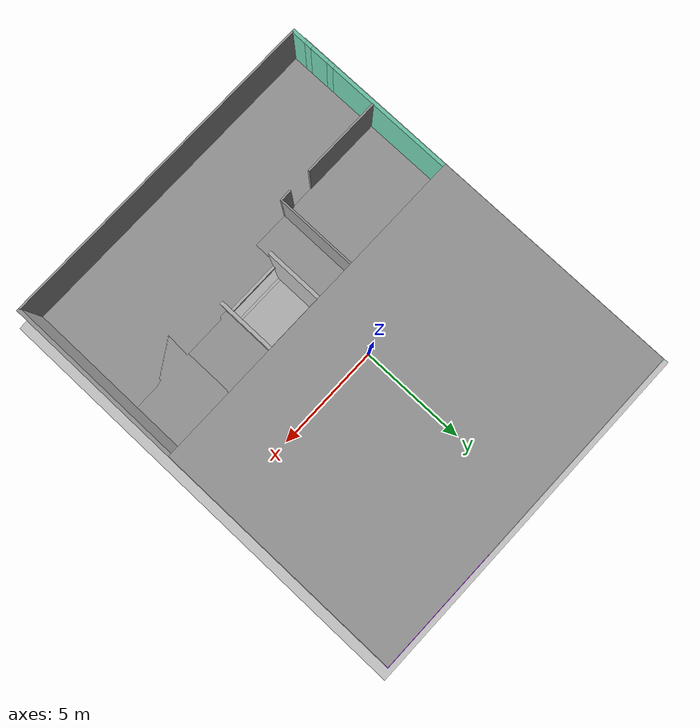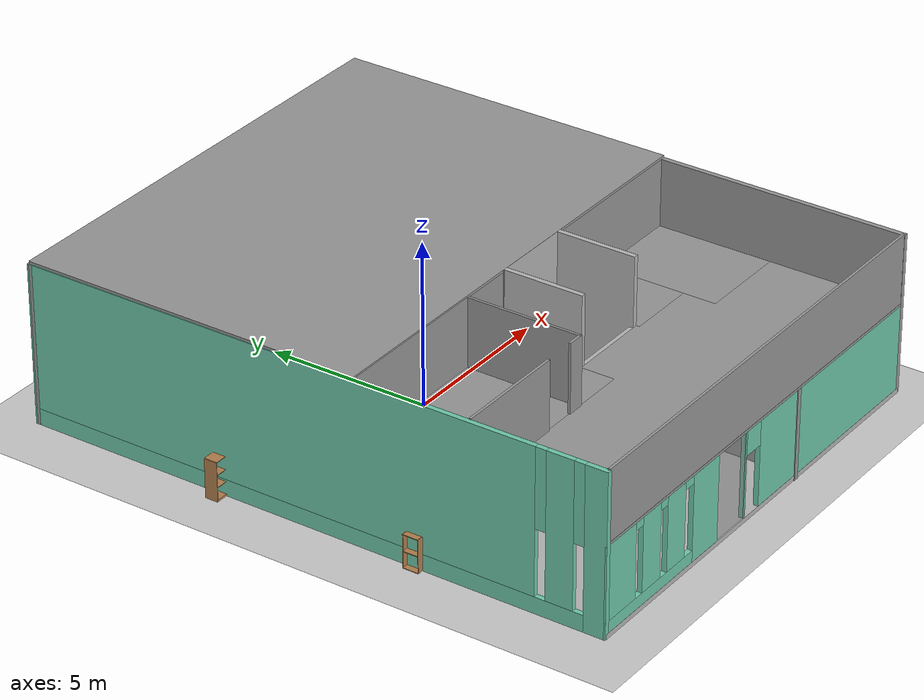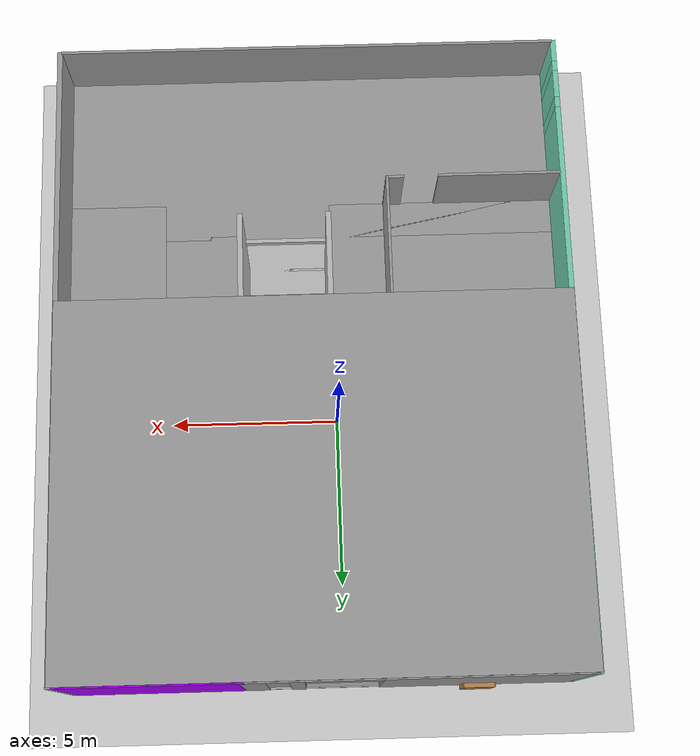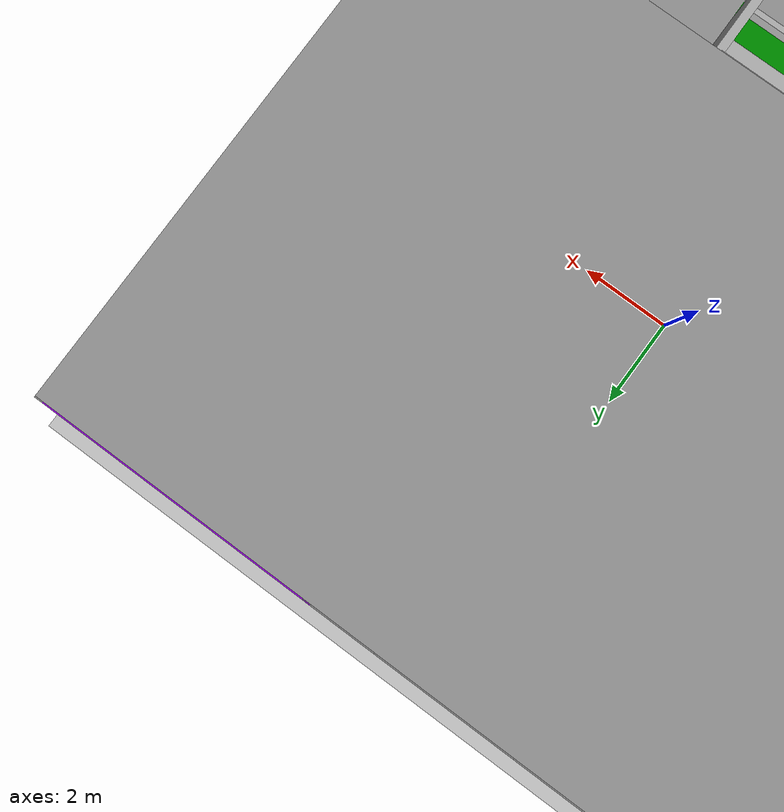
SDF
<sdf version="1.6">
 <world name="default">
  <light name="sun" type="directional">
   <pose>0 0 15 0 -0 0</pose>
   <diffuse>1 1 1 1</diffuse>
   <specular>0.1 0.1 0.1 1</specular>
   <attenuation>
    <range>1000</range>
    <constant>0.9</constant>
    <linear>0.01</linear>
    <quadratic>0.001</quadratic>
   </attenuation>
   <direction>-0.5 0.5 -1</direction>
  </light>
  <model name="ground_plane">
   <static>1</static>
   <link name="link">
    <collision name="collision">
     <geometry><plane><normal>0 0 1</normal><size>100 100</size></plane></geometry>
     <surface><friction><ode><mu>100</mu><mu2>50</mu2></ode></friction></surface>
    </collision>
    <visual name="visual">
     <cast_shadows>0</cast_shadows>
     <geometry><plane><normal>0 0 1</normal><size>100 100</size></plane></geometry>
     <material>
      <script><uri>file://media/materials/scripts/gazebo.material</uri><name>Gazebo/Grey</name></script>
     </material>
    </visual>
   </link>
  </model>
  <gravity>0 0 -9.8</gravity>
  <magnetic_field>6e-06 2.3e-05 -4.2e-05</magnetic_field>
  <atmosphere type="adiabatic"/>
  <physics name="default_physics" default="0" type="ode">
   <max_step_size>0.001</max_step_size>
   <real_time_factor>1</real_time_factor>
   <real_time_update_rate>1000</real_time_update_rate>
  </physics>
  <scene><ambient>0.4 0.4 0.4 1</ambient><background>0.7 0.7 0.7 1</background><shadows>1</shadows></scene>
  <spherical_coordinates>
   <surface_model>EARTH_WGS84</surface_model>
   <latitude_deg>0</latitude_deg>
   <longitude_deg>0</longitude_deg>
   <elevation>0</elevation>
   <heading_deg>0</heading_deg>
  </spherical_coordinates>
  <model name="osrf_elevator">
   <link name="Wall_0">
    <pose>-7.17647 0.013004 0 0 -0 1.57174</pose>
    <visual name="Wall_0_Visual_0">
     <meta><layer>0</layer></meta>
     <pose>-8.72596 0 2.4385 0 -0 0</pose>
     <geometry><box><size>0.663656 0.15 4.877</size></box></geometry>
     <material>
      <script><uri>file://media/materials/scripts/gazebo.material</uri><name>Gazebo/Grey</name></script>
      <ambient>0.435294 0.796078 0.67451 1</ambient>
     </material>
    </visual>
    <collision name="Wall_0_Collision_0">
     <geometry><box><size>0.663656 0.15 4.877</size></box></geometry>
     <pose>-8.72596 0 2.4385 0 -0 0</pose>
    </collision>
    <visual name="Wall_0_Visual_1">
     <meta><layer>0</layer></meta>
     <pose>0.331828 0 0.25 0 -0 0</pose>
     <geometry><box><size>17.4519 0.15 0.5</size></box></geometry>
     <material>
      <script><uri>file://media/materials/scripts/gazebo.material</uri><name>Gazebo/Grey</name></script>
      <ambient>0.435294 0.796078 0.67451 1</ambient>
     </material>
    </visual>
    <collision name="Wall_0_Collision_1">
     <geometry><box><size>17.4519 0.15 0.5</size></box></geometry>
     <pose>0.331828 0 0.25 0 -0 0</pose>
    </collision>
    <visual name="Wall_0_Visual_2">
     <meta><layer>0</layer></meta>
     <pose>-7.67281 0 2.6885 0 -0 0</pose>
     <geometry><box><size>0.816657 0.15 4.377</size></box></geometry>
     <material>
      <script><uri>file://media/materials/scripts/gazebo.material</uri><name>Gazebo/Grey</name></script>
      <ambient>0.435294 0.796078 0.67451 1</ambient>
     </material>
    </visual>
    <collision name="Wall_0_Collision_2">
     <geometry><box><size>0.816657 0.15 4.377</size></box></geometry>
     <pose>-7.67281 0 2.6885 0 -0 0</pose>
    </collision>
    <visual name="Wall_0_Visual_3">
     <meta><layer>0</layer></meta>
     <pose>1.05709 0 2.6885 0 -0 0</pose>
     <geometry><box><size>16.0014 0.15 4.377</size></box></geometry>
     <material>
      <script><uri>file://media/materials/scripts/gazebo.material</uri><name>Gazebo/Grey</name></script>
      <ambient>0.435294 0.796078 0.67451 1</ambient>
     </material>
    </visual>
    <collision name="Wall_0_Collision_3">
     <geometry><box><size>16.0014 0.15 4.377</size></box></geometry>
     <pose>1.05709 0 2.6885 0 -0 0</pose>
    </collision>
    <visual name="Wall_0_Visual_4">
     <meta><layer>0</layer></meta>
     <pose>-8.23763 0 3.6885 0 -0 0</pose>
     <geometry><box><size>0.313 0.15 2.377</size></box></geometry>
     <material>
      <script><uri>file://media/materials/scripts/gazebo.material</uri><name>Gazebo/Grey</name></script>
      <ambient>0.435294 0.796078 0.67451 1</ambient>
     </material>
    </visual>
    <collision name="Wall_0_Collision_4">
     <geometry><box><size>0.313 0.15 2.377</size></box></geometry>
     <pose>-8.23763 0 3.6885 0 -0 0</pose>
    </collision>
    <visual name="Wall_0_Visual_5">
     <meta><layer>0</layer></meta>
     <pose>-7.10405 0 3.6885 0 -0 0</pose>
     <geometry><box><size>0.320861 0.15 2.377</size></box></geometry>
     <material>
      <script><uri>file://media/materials/scripts/gazebo.material</uri><name>Gazebo/Grey</name></script>
      <ambient>0.435294 0.796078 0.67451 1</ambient>
     </material>
    </visual>
    <collision name="Wall_0_Collision_5">
     <geometry><box><size>0.320861 0.15 2.377</size></box></geometry>
     <pose>-7.10405 0 3.6885 0 -0 0</pose>
    </collision>
   </link>
   <link name="Wall_10">
    <pose>3.11003 -4.9485 0 0 -0 0</pose>
    <visual name="Wall_10_Visual_0">
     <meta><layer>0</layer></meta>
     <pose>-1.73626 0 1.3715 0 -0 0</pose>
     <geometry><box><size>4.52747 0.15 2.743</size></box></geometry>
     <material>
      <script><uri>file://media/materials/scripts/gazebo.material</uri><name>Gazebo/Grey</name></script>
      <ambient>0 0.666667 0 1</ambient>
     </material>
    </visual>
    <collision name="Wall_10_Collision_0">
     <geometry><box><size>4.52747 0.15 2.743</size></box></geometry>
     <pose>-1.73626 0 1.3715 0 -0 0</pose>
    </collision>
    <visual name="Wall_10_Visual_1">
     <meta><layer>0</layer></meta>
     <pose>2.58694 0 1.3715 0 -0 0</pose>
     <geometry><box><size>2.82611 0.15 2.743</size></box></geometry>
     <material>
      <script><uri>file://media/materials/scripts/gazebo.material</uri><name>Gazebo/Grey</name></script>
      <ambient>0 0.666667 0 1</ambient>
     </material>
    </visual>
    <collision name="Wall_10_Collision_1">
     <geometry><box><size>2.82611 0.15 2.743</size></box></geometry>
     <pose>2.58694 0 1.3715 0 -0 0</pose>
    </collision>
    <visual name="Wall_10_Visual_2">
     <meta><layer>0</layer></meta>
     <pose>0.85068 0 2.3715 0 -0 0</pose>
     <geometry><box><size>0.646413 0.15 0.743</size></box></geometry>
     <material>
      <script><uri>file://media/materials/scripts/gazebo.material</uri><name>Gazebo/Grey</name></script>
      <ambient>0 0.666667 0 1</ambient>
     </material>
    </visual>
    <collision name="Wall_10_Collision_2">
     <geometry><box><size>0.646413 0.15 0.743</size></box></geometry>
     <pose>0.85068 0 2.3715 0 -0 0</pose>
    </collision>
   </link>
   <link name="Wall_14">
    <pose>1.83803 -6.9775 0 0 -0 1.5708</pose>
    <visual name="Wall_14_Visual_0">
     <meta><layer>0</layer></meta>
     <pose>-0.387674 0 1.3715 0 -0 0</pose>
     <geometry><box><size>3.41138 0.15 2.743</size></box></geometry>
     <material>
      <script><uri>file://media/materials/scripts/gazebo.material</uri><name>Gazebo/Grey</name></script>
      <ambient>1 1 1 1</ambient>
     </material>
    </visual>
    <collision name="Wall_14_Collision_0">
     <geometry><box><size>3.41138 0.15 2.743</size></box></geometry>
     <pose>-0.387674 0 1.3715 0 -0 0</pose>
    </collision>
    <visual name="Wall_14_Visual_1">
     <meta><layer>0</layer></meta>
     <pose>2.00133 0 1.3715 0 -0 0</pose>
     <geometry><box><size>0.184063 0.15 2.743</size></box></geometry>
     <material>
      <script><uri>file://media/materials/scripts/gazebo.material</uri><name>Gazebo/Grey</name></script>
      <ambient>1 1 1 1</ambient>
     </material>
    </visual>
    <collision name="Wall_14_Collision_1">
     <geometry><box><size>0.184063 0.15 2.743</size></box></geometry>
     <pose>2.00133 0 1.3715 0 -0 0</pose>
    </collision>
    <visual name="Wall_14_Visual_2">
     <meta><layer>0</layer></meta>
     <pose>1.61366 0 2.3715 0 -0 0</pose>
     <geometry><box><size>0.591285 0.15 0.743</size></box></geometry>
     <material>
      <script><uri>file://media/materials/scripts/gazebo.material</uri><name>Gazebo/Grey</name></script>
      <ambient>1 1 1 1</ambient>
     </material>
    </visual>
    <collision name="Wall_14_Collision_2">
     <geometry><box><size>0.591285 0.15 0.743</size></box></geometry>
     <pose>1.61366 0 2.3715 0 -0 0</pose>
    </collision>
   </link>
   <link name="Wall_16">
    <collision name="Wall_16_Collision">
     <geometry><box><size>5.12727 0.15 2.743</size></box></geometry>
     <pose>0 0 1.3715 0 -0 0</pose>
    </collision>
    <visual name="Wall_16_Visual">
     <meta><layer>0</layer></meta>
     <pose>0 0 1.3715 0 -0 0</pose>
     <geometry><box><size>5.12727 0.15 2.743</size></box></geometry>
     <material>
      <script><uri>file://media/materials/scripts/gazebo.material</uri><name>Gazebo/Grey</name></script>
      <ambient>1 1 1 1</ambient>
     </material>
    </visual>
    <pose>-4.68247 -1.4425 0 0 -0 0</pose>
   </link>
   <link name="Wall_17">
    <pose>-2.19097 -3.185 0 0 0 -1.56907</pose>
    <visual name="Wall_17_Visual_0">
     <meta><layer>0</layer></meta>
     <pose>-1.22855 0 1.3715 0 -0 0</pose>
     <geometry><box><size>1.17851 0.15 2.743</size></box></geometry>
     <material>
      <script><uri>file://media/materials/scripts/gazebo.material</uri><name>Gazebo/Grey</name></script>
      <ambient>1 1 1 1</ambient>
     </material>
    </visual>
    <collision name="Wall_17_Collision_0">
     <geometry><box><size>1.17851 0.15 2.743</size></box></geometry>
     <pose>-1.22855 0 1.3715 0 -0 0</pose>
    </collision>
    <visual name="Wall_17_Visual_1">
     <meta><layer>0</layer></meta>
     <pose>0.886237 0 1.3715 0 -0 0</pose>
     <geometry><box><size>1.86314 0.15 2.743</size></box></geometry>
     <material>
      <script><uri>file://media/materials/scripts/gazebo.material</uri><name>Gazebo/Grey</name></script>
      <ambient>1 1 1 1</ambient>
     </material>
    </visual>
    <collision name="Wall_17_Collision_1">
     <geometry><box><size>1.86314 0.15 2.743</size></box></geometry>
     <pose>0.886237 0 1.3715 0 -0 0</pose>
    </collision>
    <visual name="Wall_17_Visual_2">
     <meta><layer>0</layer></meta>
     <pose>1.18873 0 1.3715 0 -0 0</pose>
     <geometry><box><size>1.25815 0.15 2.743</size></box></geometry>
     <material>
      <script><uri>file://media/materials/scripts/gazebo.material</uri><name>Gazebo/Grey</name></script>
      <ambient>1 1 1 1</ambient>
     </material>
    </visual>
    <collision name="Wall_17_Collision_2">
     <geometry><box><size>1.25815 0.15 2.743</size></box></geometry>
     <pose>1.18873 0 1.3715 0 -0 0</pose>
    </collision>
    <visual name="Wall_17_Visual_3">
     <meta><layer>0</layer></meta>
     <pose>-0.345304 0 2.3715 0 -0 0</pose>
     <geometry><box><size>0.587991 0.15 0.743</size></box></geometry>
     <material>
      <script><uri>file://media/materials/scripts/gazebo.material</uri><name>Gazebo/Grey</name></script>
      <ambient>1 1 1 1</ambient>
     </material>
    </visual>
    <collision name="Wall_17_Collision_3">
     <geometry><box><size>0.587991 0.15 0.743</size></box></geometry>
     <pose>-0.345304 0 2.3715 0 -0 0</pose>
    </collision>
   </link>
   <link name="Wall_18">
    <collision name="Wall_18_Collision">
     <geometry><box><size>5 0.15 2.743</size></box></geometry>
     <pose>0 0 1.3715 0 -0 0</pose>
    </collision>
    <visual name="Wall_18_Visual">
     <meta><layer>0</layer></meta>
     <pose>0 0 1.3715 0 -0 0</pose>
     <geometry><box><size>5 0.15 2.743</size></box></geometry>
     <material>
      <script><uri>file://media/materials/scripts/gazebo.material</uri><name>Gazebo/Grey</name></script>
      <ambient>1 1 1 1</ambient>
     </material>
    </visual>
    <pose>-4.61297 -4.9275 0 0 -0 3.14159</pose>
   </link>
   <link name="Wall_20">
    <collision name="Wall_20_Collision">
     <geometry><box><size>2.88731 0.15 2.743</size></box></geometry>
     <pose>0 0 1.3715 0 -0 0</pose>
    </collision>
    <visual name="Wall_20_Visual">
     <meta><layer>0</layer></meta>
     <pose>0 0 1.3715 0 -0 0</pose>
     <geometry><box><size>2.88731 0.15 2.743</size></box></geometry>
     <material>
      <script><uri>file://media/materials/scripts/gazebo.material</uri><name>Gazebo/Grey</name></script>
      <ambient>1 1 1 1</ambient>
     </material>
    </visual>
    <pose>5.74253 1.037 0 0 0 -3.1383</pose>
   </link>
   <link name="Wall_21">
    <pose>4.37403 -1.8925 0 0 0 -1.5708</pose>
    <visual name="Wall_21_Visual_0">
     <meta><layer>0</layer></meta>
     <pose>-2.34405 0 1.3715 0 -0 0</pose>
     <geometry><box><size>1.3119 0.15 2.743</size></box></geometry>
     <material>
      <script><uri>file://media/materials/scripts/gazebo.material</uri><name>Gazebo/Grey</name></script>
      <ambient>1 1 1 1</ambient>
     </material>
    </visual>
    <collision name="Wall_21_Collision_0">
     <geometry><box><size>1.3119 0.15 2.743</size></box></geometry>
     <pose>-2.34405 0 1.3715 0 -0 0</pose>
    </collision>
    <visual name="Wall_21_Visual_1">
     <meta><layer>0</layer></meta>
     <pose>-0.970323 0 1.3715 0 -0 0</pose>
     <geometry><box><size>0.213619 0.15 2.743</size></box></geometry>
     <material>
      <script><uri>file://media/materials/scripts/gazebo.material</uri><name>Gazebo/Grey</name></script>
      <ambient>1 1 1 1</ambient>
     </material>
    </visual>
    <collision name="Wall_21_Collision_1">
     <geometry><box><size>0.213619 0.15 2.743</size></box></geometry>
     <pose>-0.970323 0 1.3715 0 -0 0</pose>
    </collision>
    <visual name="Wall_21_Visual_2">
     <meta><layer>0</layer></meta>
     <pose>0.938748 0 1.3715 0 -0 0</pose>
     <geometry><box><size>2.36558 0.15 2.743</size></box></geometry>
     <material>
      <script><uri>file://media/materials/scripts/gazebo.material</uri><name>Gazebo/Grey</name></script>
      <ambient>1 1 1 1</ambient>
     </material>
    </visual>
    <collision name="Wall_21_Collision_2">
     <geometry><box><size>2.36558 0.15 2.743</size></box></geometry>
     <pose>0.938748 0 1.3715 0 -0 0</pose>
    </collision>
    <visual name="Wall_21_Visual_3">
     <meta><layer>0</layer></meta>
     <pose>2.89346 0 1.3715 0 -0 0</pose>
     <geometry><box><size>0.213086 0.15 2.743</size></box></geometry>
     <material>
      <script><uri>file://media/materials/scripts/gazebo.material</uri><name>Gazebo/Grey</name></script>
      <ambient>1 1 1 1</ambient>
     </material>
    </visual>
    <collision name="Wall_21_Collision_3">
     <geometry><box><size>0.213086 0.15 2.743</size></box></geometry>
     <pose>2.89346 0 1.3715 0 -0 0</pose>
    </collision>
    <visual name="Wall_21_Visual_4">
     <meta><layer>0</layer></meta>
     <pose>-1.38262 0 2.3715 0 -0 0</pose>
     <geometry><box><size>0.610969 0.15 0.743</size></box></geometry>
     <material>
      <script><uri>file://media/materials/scripts/gazebo.material</uri><name>Gazebo/Grey</name></script>
      <ambient>1 1 1 1</ambient>
     </material>
    </visual>
    <collision name="Wall_21_Collision_4">
     <geometry><box><size>0.610969 0.15 0.743</size></box></geometry>
     <pose>-1.38262 0 2.3715 0 -0 0</pose>
    </collision>
    <visual name="Wall_21_Visual_5">
     <meta><layer>0</layer></meta>
     <pose>-0.553779 0 2.3715 0 -0 0</pose>
     <geometry><box><size>0.61947 0.15 0.743</size></box></geometry>
     <material>
      <script><uri>file://media/materials/scripts/gazebo.material</uri><name>Gazebo/Grey</name></script>
      <ambient>1 1 1 1</ambient>
     </material>
    </visual>
    <collision name="Wall_21_Collision_5">
     <geometry><box><size>0.61947 0.15 0.743</size></box></geometry>
     <pose>-0.553779 0 2.3715 0 -0 0</pose>
    </collision>
    <visual name="Wall_21_Visual_6">
     <meta><layer>0</layer></meta>
     <pose>2.45423 0 2.3715 0 -0 0</pose>
     <geometry><box><size>0.665375 0.15 0.743</size></box></geometry>
     <material>
      <script><uri>file://media/materials/scripts/gazebo.material</uri><name>Gazebo/Grey</name></script>
      <ambient>1 1 1 1</ambient>
     </material>
    </visual>
    <collision name="Wall_21_Collision_6">
     <geometry><box><size>0.665375 0.15 0.743</size></box></geometry>
     <pose>2.45423 0 2.3715 0 -0 0</pose>
    </collision>
   </link>
   <link name="Wall_23">
    <collision name="Wall_23_Collision">
     <geometry><box><size>2.75 0.15 2.743</size></box></geometry>
     <pose>0 0 1.3715 0 -0 0</pose>
    </collision>
    <visual name="Wall_23_Visual">
     <meta><layer>0</layer></meta>
     <pose>0 0 1.3715 0 -0 0</pose>
     <geometry><box><size>2.75 0.15 2.743</size></box></geometry>
     <material>
      <script><uri>file://media/materials/scripts/gazebo.material</uri><name>Gazebo/Grey</name></script>
      <ambient>1 1 1 1</ambient>
     </material>
    </visual>
    <pose>5.74203 -2.9565 0 0 -0 0</pose>
   </link>
   <link name="Wall_25">
    <collision name="Wall_25_Collision">
     <geometry><box><size>2.75 0.15 2.743</size></box></geometry>
     <pose>0 0 1.3715 0 -0 0</pose>
    </collision>
    <visual name="Wall_25_Visual">
     <meta><layer>0</layer></meta>
     <pose>0 0 1.3715 0 -0 0</pose>
     <geometry><box><size>2.75 0.15 2.743</size></box></geometry>
     <material>
      <script><uri>file://media/materials/scripts/gazebo.material</uri><name>Gazebo/Grey</name></script>
      <ambient>1 1 1 1</ambient>
     </material>
    </visual>
    <pose>5.76203 -0.932496 0 0 -0 0</pose>
   </link>
   <link name="Wall_27">
    <collision name="Wall_27_Collision">
     <geometry><box><size>4 0.15 2.743</size></box></geometry>
     <pose>0 0 1.3715 0 -0 0</pose>
    </collision>
    <visual name="Wall_27_Visual">
     <meta><layer>0</layer></meta>
     <pose>0 0 1.3715 0 -0 0</pose>
     <geometry><box><size>4 0.15 2.743</size></box></geometry>
     <material>
      <script><uri>file://media/materials/scripts/gazebo.material</uri><name>Gazebo/Grey</name></script>
      <ambient>1 1 1 1</ambient>
     </material>
    </visual>
    <pose>4.75503 -7.0125 0 0 -0 1.5708</pose>
   </link>
   <link name="Wall_29">
    <collision name="Wall_29_Collision">
     <geometry><box><size>1.39187 0.15 4.877</size></box></geometry>
     <pose>0 0 2.4385 0 -0 0</pose>
    </collision>
    <visual name="Wall_29_Visual">
     <meta><layer>0</layer></meta>
     <pose>0 0 2.4385 0 -0 0</pose>
     <geometry><box><size>1.39187 0.15 4.877</size></box></geometry>
     <material>
      <script><uri>file://media/materials/scripts/gazebo.material</uri><name>Gazebo/Grey</name></script>
      <ambient>0.996078 0.47451 0.0196078 1</ambient>
     </material>
    </visual>
    <pose>-6.49697 4.1045 0 0 -0 0</pose>
   </link>
   <link name="Wall_30">
    <collision name="Wall_30_Collision">
     <geometry><box><size>3 0.15 4.877</size></box></geometry>
     <pose>0 0 2.4385 0 -0 0</pose>
    </collision>
    <visual name="Wall_30_Visual">
     <meta><layer>0</layer></meta>
     <pose>0 0 2.4385 0 -0 0</pose>
     <geometry><box><size>3 0.15 4.877</size></box></geometry>
     <material>
      <script><uri>file://media/materials/scripts/gazebo.material</uri><name>Gazebo/Grey</name></script>
      <ambient>1 1 1 1</ambient>
     </material>
    </visual>
    <pose>-5.87597 5.5295 0 0 -0 1.5708</pose>
   </link>
   <link name="Wall_31">
    <pose>-6.50397 6.9525 0 0 0 -3.13841</pose>
    <visual name="Wall_31_Visual_0">
     <meta><layer>0</layer></meta>
     <pose>-0.567544 0 2.4385 0 -0 0</pose>
     <geometry><box><size>0.271575 0.15 4.877</size></box></geometry>
     <material>
      <script><uri>file://media/materials/scripts/gazebo.material</uri><name>Gazebo/Grey</name></script>
      <ambient>1 1 1 1</ambient>
     </material>
    </visual>
    <collision name="Wall_31_Collision_0">
     <geometry><box><size>0.271575 0.15 4.877</size></box></geometry>
     <pose>-0.567544 0 2.4385 0 -0 0</pose>
    </collision>
    <visual name="Wall_31_Visual_1">
     <meta><layer>0</layer></meta>
     <pose>0.441678 0 2.4385 0 -0 0</pose>
     <geometry><box><size>0.523307 0.15 4.877</size></box></geometry>
     <material>
      <script><uri>file://media/materials/scripts/gazebo.material</uri><name>Gazebo/Grey</name></script>
      <ambient>1 1 1 1</ambient>
     </material>
    </visual>
    <collision name="Wall_31_Collision_1">
     <geometry><box><size>0.523307 0.15 4.877</size></box></geometry>
     <pose>0.441678 0 2.4385 0 -0 0</pose>
    </collision>
    <visual name="Wall_31_Visual_3">
     <meta><layer>0</layer></meta>
     <pose>-0.125866 0 3.4385 0 -0 0</pose>
     <geometry><box><size>0.611781 0.15 2.877</size></box></geometry>
     <material>
      <script><uri>file://media/materials/scripts/gazebo.material</uri><name>Gazebo/Grey</name></script>
      <ambient>1 1 1 1</ambient>
     </material>
    </visual>
    <collision name="Wall_31_Collision_3">
     <geometry><box><size>0.611781 0.15 2.877</size></box></geometry>
     <pose>-0.125866 0 3.4385 0 -0 0</pose>
    </collision>
   </link>
   <link name="Wall_35">
    <pose>-2.50997 8.9955 0 0 -0 0</pose>
    <visual name="Wall_35_Visual_0">
     <meta><layer>0</layer></meta>
     <pose>-1.92197 0 2.4385 0 -0 0</pose>
     <geometry><box><size>5.65606 0.15 4.877</size></box></geometry>
     <material>
      <script><uri>file://media/materials/scripts/gazebo.material</uri><name>Gazebo/Grey</name></script>
      <ambient>1 1 1 1</ambient>
     </material>
    </visual>
    <collision name="Wall_35_Collision_0">
     <geometry><box><size>5.65606 0.15 4.877</size></box></geometry>
     <pose>-1.92197 0 2.4385 0 -0 0</pose>
    </collision>
    <visual name="Wall_35_Visual_1">
     <meta><layer>0</layer></meta>
     <pose>3.22541 0 2.4385 0 -0 0</pose>
     <geometry><box><size>0.406701 0.15 4.877</size></box></geometry>
     <material>
      <script><uri>file://media/materials/scripts/gazebo.material</uri><name>Gazebo/Grey</name></script>
      <ambient>1 1 1 1</ambient>
     </material>
    </visual>
    <collision name="Wall_35_Collision_1">
     <geometry><box><size>0.406701 0.15 4.877</size></box></geometry>
     <pose>3.22541 0 2.4385 0 -0 0</pose>
    </collision>
    <visual name="Wall_35_Visual_2">
     <meta><layer>0</layer></meta>
     <pose>4.40208 0 2.4385 0 -0 0</pose>
     <geometry><box><size>0.695843 0.15 4.877</size></box></geometry>
     <material>
      <script><uri>file://media/materials/scripts/gazebo.material</uri><name>Gazebo/Grey</name></script>
      <ambient>1 1 1 1</ambient>
     </material>
    </visual>
    <collision name="Wall_35_Collision_2">
     <geometry><box><size>0.695843 0.15 4.877</size></box></geometry>
     <pose>4.40208 0 2.4385 0 -0 0</pose>
    </collision>
    <visual name="Wall_35_Visual_5">
     <meta><layer>0</layer></meta>
     <pose>3.74146 0 3.4385 0 -0 0</pose>
     <geometry><box><size>0.625391 0.15 2.877</size></box></geometry>
     <material>
      <script><uri>file://media/materials/scripts/gazebo.material</uri><name>Gazebo/Grey</name></script>
      <ambient>1 1 1 1</ambient>
     </material>
    </visual>
    <collision name="Wall_35_Collision_5">
     <geometry><box><size>0.625391 0.15 2.877</size></box></geometry>
     <pose>3.74146 0 3.4385 0 -0 0</pose>
    </collision>
    <visual name="Wall_35_Visual_6">
     <meta><layer>0</layer></meta>
     <pose>1.96406 0 4.4385 0 -0 0</pose>
     <geometry><box><size>2.116 0.15 0.877</size></box></geometry>
     <material>
      <script><uri>file://media/materials/scripts/gazebo.material</uri><name>Gazebo/Grey</name></script>
      <ambient>1 1 1 1</ambient>
     </material>
    </visual>
    <collision name="Wall_35_Collision_6">
     <geometry><box><size>2.116 0.15 0.877</size></box></geometry>
     <pose>1.96406 0 4.4385 0 -0 0</pose>
    </collision>
   </link>
   <link name="Wall_36">
    <collision name="Wall_36_Collision">
     <geometry><box><size>5.17 0.15 4.877</size></box></geometry>
     <pose>0 0 2.4385 0 -0 0</pose>
    </collision>
    <visual name="Wall_36_Visual">
     <meta><layer>0</layer></meta>
     <pose>0 0 2.4385 0 -0 0</pose>
     <geometry><box><size>5.17 0.15 4.877</size></box></geometry>
     <material>
      <script><uri>file://media/materials/scripts/gazebo.material</uri><name>Gazebo/Grey</name></script>
      <ambient>0.666667 0 1 1</ambient>
     </material>
    </visual>
    <pose>4.67503 8.9955 0 0 -0 0</pose>
   </link>
   <link name="Wall_5">
    <collision name="Wall_5_Collision">
     <geometry><box><size>18.1152 0.15 4.877</size></box></geometry>
     <pose>0 0 2.4385 0 -0 0</pose>
    </collision>
    <visual name="Wall_5_Visual">
     <meta><layer>0</layer></meta>
     <pose>0 0 2.4385 0 -0 0</pose>
     <geometry><box><size>18.1152 0.15 4.877</size></box></geometry>
     <material>
      <script><uri>file://media/materials/scripts/gazebo.material</uri><name>Gazebo/Grey</name></script>
      <ambient>1 1 1 1</ambient>
     </material>
    </visual>
    <pose>7.18353 0.013004 0 0 0 -1.57096</pose>
   </link>
   <link name="Wall_6">
    <pose>0.007029 -8.9695 0 0 -0 3.14159</pose>
    <visual name="Wall_6_Visual_0">
     <meta><layer>0</layer></meta>
     <pose>-3.60425 0 1.365 0 -0 0</pose>
     <geometry><box><size>7.2915 0.15 2.73</size></box></geometry>
     <material>
      <script><uri>file://media/materials/scripts/gazebo.material</uri><name>Gazebo/Grey</name></script>
      <ambient>0.435294 0.796078 0.67451 1</ambient>
     </material>
    </visual>
    <collision name="Wall_6_Collision_0">
     <geometry><box><size>7.2915 0.15 2.73</size></box></geometry>
     <pose>-3.60425 0 1.365 0 -0 0</pose>
    </collision>
    <visual name="Wall_6_Visual_1">
     <meta><layer>0</layer></meta>
     <pose>0.726241 0 1.365 0 -0 0</pose>
     <geometry><box><size>0.056893 0.15 2.73</size></box></geometry>
     <material>
      <script><uri>file://media/materials/scripts/gazebo.material</uri><name>Gazebo/Grey</name></script>
      <ambient>0.435294 0.796078 0.67451 1</ambient>
     </material>
    </visual>
    <collision name="Wall_6_Collision_1">
     <geometry><box><size>0.056893 0.15 2.73</size></box></geometry>
     <pose>0.726241 0 1.365 0 -0 0</pose>
    </collision>
    <visual name="Wall_6_Visual_2">
     <meta><layer>0</layer></meta>
     <pose>2.65105 0 1.365 0 -0 0</pose>
     <geometry><box><size>1.19273 0.15 2.73</size></box></geometry>
     <material>
      <script><uri>file://media/materials/scripts/gazebo.material</uri><name>Gazebo/Grey</name></script>
      <ambient>0.435294 0.796078 0.67451 1</ambient>
     </material>
    </visual>
    <collision name="Wall_6_Collision_2">
     <geometry><box><size>1.19273 0.15 2.73</size></box></geometry>
     <pose>2.65105 0 1.365 0 -0 0</pose>
    </collision>
    <visual name="Wall_6_Visual_4">
     <meta><layer>0</layer></meta>
     <pose>5.24871 0 0.25 0 -0 0</pose>
     <geometry><box><size>4.00258 0.15 0.5</size></box></geometry>
     <material>
      <script><uri>file://media/materials/scripts/gazebo.material</uri><name>Gazebo/Grey</name></script>
      <ambient>0.435294 0.796078 0.67451 1</ambient>
     </material>
    </visual>
    <collision name="Wall_6_Collision_4">
     <geometry><box><size>4.00258 0.15 0.5</size></box></geometry>
     <pose>5.24871 0 0.25 0 -0 0</pose>
    </collision>
    <visual name="Wall_6_Visual_5">
     <meta><layer>0</layer></meta>
     <pose>4.0419 0 1.615 0 -0 0</pose>
     <geometry><box><size>0.828969 0.15 2.23</size></box></geometry>
     <material>
      <script><uri>file://media/materials/scripts/gazebo.material</uri><name>Gazebo/Grey</name></script>
      <ambient>0.435294 0.796078 0.67451 1</ambient>
     </material>
    </visual>
    <collision name="Wall_6_Collision_5">
     <geometry><box><size>0.828969 0.15 2.23</size></box></geometry>
     <pose>4.0419 0 1.615 0 -0 0</pose>
    </collision>
    <visual name="Wall_6_Visual_6">
     <meta><layer>0</layer></meta>
     <pose>5.18099 0 1.615 0 -0 0</pose>
     <geometry><box><size>0.819207 0.15 2.23</size></box></geometry>
     <material>
      <script><uri>file://media/materials/scripts/gazebo.material</uri><name>Gazebo/Grey</name></script>
      <ambient>0.435294 0.796078 0.67451 1</ambient>
     </material>
    </visual>
    <collision name="Wall_6_Collision_6">
     <geometry><box><size>0.819207 0.15 2.23</size></box></geometry>
     <pose>5.18099 0 1.615 0 -0 0</pose>
    </collision>
    <visual name="Wall_6_Visual_7">
     <meta><layer>0</layer></meta>
     <pose>6.58056 0 1.615 0 -0 0</pose>
     <geometry><box><size>1.33888 0.15 2.23</size></box></geometry>
     <material>
      <script><uri>file://media/materials/scripts/gazebo.material</uri><name>Gazebo/Grey</name></script>
      <ambient>0.435294 0.796078 0.67451 1</ambient>
     </material>
    </visual>
    <collision name="Wall_6_Collision_7">
     <geometry><box><size>1.33888 0.15 2.23</size></box></geometry>
     <pose>6.58056 0 1.615 0 -0 0</pose>
    </collision>
    <visual name="Wall_6_Visual_8">
     <meta><layer>0</layer></meta>
     <pose>0.369648 0 2.365 0 -0 0</pose>
     <geometry><box><size>0.656294 0.15 0.73</size></box></geometry>
     <material>
      <script><uri>file://media/materials/scripts/gazebo.material</uri><name>Gazebo/Grey</name></script>
      <ambient>0.435294 0.796078 0.67451 1</ambient>
     </material>
    </visual>
    <collision name="Wall_6_Collision_8">
     <geometry><box><size>0.656294 0.15 0.73</size></box></geometry>
     <pose>0.369648 0 2.365 0 -0 0</pose>
    </collision>
    <visual name="Wall_6_Visual_9">
     <meta><layer>0</layer></meta>
     <pose>3.43742 0 2.615 0 -0 0</pose>
     <geometry><box><size>0.38 0.15 0.23</size></box></geometry>
     <material>
      <script><uri>file://media/materials/scripts/gazebo.material</uri><name>Gazebo/Grey</name></script>
      <ambient>0.435294 0.796078 0.67451 1</ambient>
     </material>
    </visual>
    <collision name="Wall_6_Collision_9">
     <geometry><box><size>0.38 0.15 0.23</size></box></geometry>
     <pose>3.43742 0 2.615 0 -0 0</pose>
    </collision>
    <visual name="Wall_6_Visual_10">
     <meta><layer>0</layer></meta>
     <pose>4.61389 0 2.615 0 -0 0</pose>
     <geometry><box><size>0.315 0.15 0.23</size></box></geometry>
     <material>
      <script><uri>file://media/materials/scripts/gazebo.material</uri><name>Gazebo/Grey</name></script>
      <ambient>0.435294 0.796078 0.67451 1</ambient>
     </material>
    </visual>
    <collision name="Wall_6_Collision_10">
     <geometry><box><size>0.315 0.15 0.23</size></box></geometry>
     <pose>4.61389 0 2.615 0 -0 0</pose>
    </collision>
    <visual name="Wall_6_Visual_11">
     <meta><layer>0</layer></meta>
     <pose>5.75086 0 2.615 0 -0 0</pose>
     <geometry><box><size>0.320532 0.15 0.23</size></box></geometry>
     <material>
      <script><uri>file://media/materials/scripts/gazebo.material</uri><name>Gazebo/Grey</name></script>
      <ambient>0.435294 0.796078 0.67451 1</ambient>
     </material>
    </visual>
    <collision name="Wall_6_Collision_11">
     <geometry><box><size>0.320532 0.15 0.23</size></box></geometry>
     <pose>5.75086 0 2.615 0 -0 0</pose>
    </collision>
   </link>
   <link name="front_window">
    <pose>-1.42369 -8.99808 1.36421 0 -0 0</pose>
    <collision name="front_window_collision">
     <geometry><box><size>1.37422 0.034702 2.72768</size></box></geometry>
    </collision>
    <visual name="front_window_visual">
     <meta><layer>0</layer></meta>
     <geometry><box><size>1.37422 0.034702 2.72768</size></box></geometry>
     <material><script><name>Gazebo/GreyTransparent</name><uri>__default__</uri></script></material>
    </visual>
   </link>
   <link name="garage_door">
    <pose>-0.536243 9 2 0 -0 0</pose>
    <collision name="collision"><geometry><box><size>2.19515 0.034702 4</size></box></geometry></collision>
    <visual name="visual">
     <meta><layer>0</layer></meta>
     <geometry><box><size>2.19151 0.034702 4</size></box></geometry>
     <material><script><name>Gazebo/GreyTransparent</name><uri>__default__</uri></script></material>
    </visual>
   </link>
   <link name="ceiling1_part1">
    <pose>0.055266 -6.45681 2.76928 0 -0 0</pose>
    <collision name="collision"><geometry><box><size>14.4026 5.175 0.078</size></box></geometry></collision>
    <visual name="visual">
     <meta><layer>1</layer></meta>
     <geometry><box><size>14.4026 5.175 0.078</size></box></geometry>
     <material><script><name>Gazebo/Grey</name><uri>__default__</uri></script></material>
    </visual>
   </link>
   <link name="ceiling1_part2">
    <pose>-3.85568 -3.13263 2.76928 0 -0 0</pose>
    <collision name="collision"><geometry><box><size>6.64939 3.53076 0.078</size></box></geometry></collision>
    <visual name="visual">
     <meta><layer>1</layer></meta>
     <geometry><box><size>6.64939 3.53076 0.078</size></box></geometry>
     <material><script><name>Gazebo/Grey</name><uri>__default__</uri></script></material>
    </visual>
   </link>
   <link name="ceiling1_part3">
    <pose>5.71297 -1.93585 2.76928 0 -0 0</pose>
    <collision name="collision"><geometry><box><size>2.82725 6.08484 0.078</size></box></geometry></collision>
    <visual name="visual">
     <meta><layer>1</layer></meta>
     <geometry><box><size>2.82725 6.08484 0.078</size></box></geometry>
     <material><script><name>Gazebo/Grey</name><uri>__default__</uri></script></material>
    </visual>
   </link>
   <link name="ceiling1_part4">
    <pose>0 3.79823 4.91588 0 -0 0</pose>
    <collision name="collision"><geometry><box><size>14.4595 10.4662 0.078</size></box></geometry></collision>
    <visual name="visual">
     <meta><layer>1</layer></meta>
     <geometry><box><size>14.4595 10.4662 0.078</size></box></geometry>
     <material><script><name>Gazebo/Grey</name><uri>__default__</uri></script></material>
    </visual>
   </link>
   <link name="floor1_part5">
    <pose>-4.65046 -1.39728 3.85794 1.5708 -0 0</pose>
    <collision name="collision"><geometry><box><size>5.03711 2.0998 0.078</size></box></geometry></collision>
    <visual name="visual">
     <meta><layer>1</layer></meta>
     <geometry><box><size>5.03711 2.0998 0.078</size></box></geometry>
     <material><script><name>Gazebo/Grey</name><uri>__default__</uri></script></material>
    </visual>
   </link>
   <link name="floor1_part6">
    <pose>5.71783 1.06705 3.85828 1.5708 -0 0</pose>
    <collision name="collision"><geometry><box><size>2.83967 2.0998 0.078</size></box></geometry></collision>
    <visual name="visual">
     <meta><layer>1</layer></meta>
     <geometry><box><size>2.83967 2.0998 0.078</size></box></geometry>
     <material><script><name>Gazebo/Grey</name><uri>__default__</uri></script></material>
    </visual>
   </link>
   <link name="floor1_part7">
    <pose>2.39941 -1.39058 3.85828 1.5708 -0 0</pose>
    <collision name="collision"><geometry><box><size>9.43026 2.0998 0.078</size></box></geometry></collision>
    <visual name="visual">
     <meta><layer>1</layer></meta>
     <geometry><box><size>9.43026 2.0998 0.078</size></box></geometry>
     <material><script><name>Gazebo/Grey</name><uri>__default__</uri></script></material>
    </visual>
   </link>
   <link name="floor1_part8">
    <pose>0 -9 3.86461 1.5708 -0 0</pose>
    <collision name="collision"><geometry><box><size>14.2592 2.0998 0.078</size></box></geometry></collision>
    <visual name="visual">
     <meta><layer>1</layer></meta>
     <geometry><box><size>14.2592 2.0998 0.078</size></box></geometry>
     <material><script><name>Gazebo/Grey</name><uri>__default__</uri></script></material>
    </visual>
   </link>
   <link name="floor1_part9">
    <pose>-5.36806 -4.90906 3.85794 1.5708 -0 0</pose>
    <collision name="collision"><geometry><box><size>3.47446 2.0998 0.078</size></box></geometry></collision>
    <visual name="visual">
     <meta><layer>1</layer></meta>
     <geometry><box><size>3.47446 2.0998 0.078</size></box></geometry>
     <material><script><name>Gazebo/Grey</name><uri>__default__</uri></script></material>
    </visual>
   </link>
   <link name="floor1_part10">
    <pose>-2.39225 -4.89435 3.85794 1.5708 -0 0</pose>
    <collision name="collision"><geometry><box><size>0.519866 2.0998 0.078</size></box></geometry></collision>
    <visual name="visual">
     <meta><layer>1</layer></meta>
     <geometry><box><size>0.519866 2.0998 0.078</size></box></geometry>
     <material><script><name>Gazebo/Grey</name><uri>__default__</uri></script></material>
    </visual>
   </link>
   <link name="floor1_part11">
    <pose>-2.17305 -3.18058 3.85794 1.5708 0 -1.5708</pose>
    <collision name="collision"><geometry><box><size>3.4917 2.0998 0.078</size></box></geometry></collision>
    <visual name="visual">
     <meta><layer>1</layer></meta>
     <geometry><box><size>3.4917 2.0998 0.078</size></box></geometry>
     <material><script><name>Gazebo/Grey</name><uri>__default__</uri></script></material>
    </visual>
   </link>
   <link name="floor1_part12">
    <pose>3.22506 -2.66914 2.76928 0 -0 0</pose>
    <collision name="collision"><geometry><box><size>2.20229 2.60169 0.078</size></box></geometry></collision>
    <visual name="visual">
     <meta><layer>1</layer></meta>
     <geometry><box><size>2.20229 2.60169 0.078</size></box></geometry>
     <material><script><name>Gazebo/Grey</name><uri>__default__</uri></script></material>
    </visual>
   </link>
   <link name="ground_floor">
    <pose>0 0 0.075 0 -0 0</pose>
    <collision name="collision">
     <geometry><box><size>14.4 18.1 0.15</size></box></geometry>
     <surface><contact><collide_bitmask>1</collide_bitmask></contact></surface>
    </collision>
    <visual name="visual"><geometry><box><size>14.4 18.1 0.15</size></box></geometry></visual>
   </link>
   <link name="elevator_shaft">
    <pose>0.781821 -2.6219 0 0 0 -1.5708</pose>
    <collision name="shaft_wall1_collision">
     <pose>0 1.25 2.4774 0 -0 0</pose>
     <geometry><box><size>2.5 0.15 4.95479</size></box></geometry>
    </collision>
    <visual name="shaft_wall1_visual">
     <pose>0 1.25 2.4774 0 -0 0</pose>
     <geometry><box><size>2.5 0.15 4.95479</size></box></geometry>
    </visual>
    <collision name="shaft_wall2_collision">
     <pose>0 -1.25 2.4774 0 -0 0</pose>
     <geometry><box><size>2.5 0.15 4.95479</size></box></geometry>
    </collision>
    <visual name="shaft_wall2_visual">
     <pose>0 -1.25 2.4774 0 -0 0</pose>
     <geometry><box><size>2.5 0.15 4.95479</size></box></geometry>
    </visual>
    <collision name="shaft_wall3_collision">
     <pose>-1.25 0 2.4774 0 -0 0</pose>
     <geometry><box><size>0.15 2.7 4.95479</size></box></geometry>
    </collision>
    <visual name="shaft_wall3_visual">
     <pose>-1.25 0 2.4774 0 -0 0</pose>
     <geometry><box><size>0.15 2.7 4.95479</size></box></geometry>
    </visual>
    <collision name="floor0_collision">
     <pose>1.19 0 0.075 0 -0 0</pose>
     <geometry><box><size>0.12 2.5 0.15</size></box></geometry>
    </collision>
    <visual name="floor0_visual">
     <pose>1.19 0 0.075 0 -0 0</pose>
     <geometry><box><size>0.12 2.5 0.15</size></box></geometry>
    </visual>
    <collision name="floor1_collision">
     <pose>1.19 0 2.70825 0 -0 0</pose>
     <geometry><box><size>0.12 2.5 0.2</size></box></geometry>
    </collision>
    <visual name="floor1_visual">
     <pose>1.19 0 2.70825 0 -0 0</pose>
     <geometry><box><size>0.12 2.5 0.2</size></box></geometry>
    </visual>
   </link>
   <static>1</static>
   <pose>0.630833 -1.09505 0 0 -0 0</pose>
  </model>
  <model name="cabinet">
   <static>1</static>
   <link name="cabinet_bottom_plate">
    <inertial>
     <pose>0 0 -1 0 -0 0</pose>
     <inertia><ixx>2.05</ixx><ixy>0</ixy><ixz>0</ixz><iyy>2.05</iyy><iyz>0</iyz><izz>2.05</izz></inertia>
     <mass>25</mass>
    </inertial>
    <collision name="cabinet_bottom_plate_geom">
     <pose>0 0 0.01 0 -0 0</pose>
     <geometry><box><size>0.45 0.45 0.02</size></box></geometry>
    </collision>
    <visual name="cabinet_bottom_plate_geom_visual">
     <pose>0 0 0.01 0 -0 0</pose>
     <geometry><box><size>0.45 0.45 0.02</size></box></geometry>
     <material>
      <script><uri>file://media/materials/scripts/gazebo.material</uri><name>Gazebo/Wood</name></script>
     </material>
    </visual>
    <collision name="cabinet_bottom_plate_geom_cabinet_back_plate">
     <pose>0.235 0 0.51 0 -0 0</pose>
     <geometry><box><size>0.02 0.45 1.02</size></box></geometry>
    </collision>
    <visual name="cabinet_bottom_plate_geom_cabinet_back_plate_visual">
     <pose>0.235 0 0.51 0 -0 0</pose>
     <geometry><box><size>0.02 0.45 1.02</size></box></geometry>
     <material>
      <script><uri>file://media/materials/scripts/gazebo.material</uri><name>Gazebo/Wood</name></script>
     </material>
    </visual>
    <collision name="cabinet_bottom_plate_geom_cabinet_left_plate">
     <pose>0 0.235 0.51 0 -0 0</pose>
     <geometry><box><size>0.45 0.02 1.02</size></box></geometry>
    </collision>
    <visual name="cabinet_bottom_plate_geom_cabinet_left_plate_visual">
     <pose>0 0.235 0.51 0 -0 0</pose>
     <geometry><box><size>0.45 0.02 1.02</size></box></geometry>
     <material>
      <script><uri>file://media/materials/scripts/gazebo.material</uri><name>Gazebo/Wood</name></script>
     </material>
    </visual>
    <collision name="cabinet_bottom_plate_geom_cabinet_middle_plate">
     <pose>0 0 0.51 0 -0 0</pose>
     <geometry><box><size>0.45 0.45 0.02</size></box></geometry>
    </collision>
    <visual name="cabinet_bottom_plate_geom_cabinet_middle_plate_visual">
     <pose>0 0 0.51 0 -0 0</pose>
     <geometry><box><size>0.45 0.45 0.02</size></box></geometry>
     <material>
      <script><uri>file://media/materials/scripts/gazebo.material</uri><name>Gazebo/Wood</name></script>
     </material>
    </visual>
    <collision name="cabinet_bottom_plate_geom_cabinet_right_plate">
     <pose>0 -0.235 0.51 0 -0 0</pose>
     <geometry><box><size>0.45 0.02 1.02</size></box></geometry>
    </collision>
    <visual name="cabinet_bottom_plate_geom_cabinet_right_plate_visual">
     <pose>0 -0.235 0.51 0 -0 0</pose>
     <geometry><box><size>0.45 0.02 1.02</size></box></geometry>
     <material>
      <script><uri>file://media/materials/scripts/gazebo.material</uri><name>Gazebo/Wood</name></script>
     </material>
    </visual>
    <collision name="cabinet_bottom_plate_geom_cabinet_top_plate">
     <pose>0 0 1.01 0 -0 0</pose>
     <geometry><box><size>0.45 0.45 0.02</size></box></geometry>
    </collision>
    <visual name="cabinet_bottom_plate_geom_cabinet_top_plate_visual">
     <pose>0 0 1.01 0 -0 0</pose>
     <geometry><box><size>0.45 0.45 0.02</size></box></geometry>
     <material>
      <script><uri>file://media/materials/scripts/gazebo.material</uri><name>Gazebo/Wood</name></script>
     </material>
    </visual>
   </link>
   <pose>-6.57618 -4.39691 0 0 -0 0</pose>
  </model>
  <model name="bookshelf">
   <static>1</static>
   <link name="link">
    <inertial><mass>1</mass></inertial>
    <collision name="back">
     <pose>0 0.005 0.6 0 -0 0</pose>
     <geometry><box><size>0.9 0.01 1.2</size></box></geometry>
    </collision>
    <visual name="visual1">
     <pose>0 0.005 0.6 0 -0 0</pose>
     <geometry><box><size>0.9 0.01 1.2</size></box></geometry>
     <material>
      <script><uri>file://media/materials/scripts/gazebo.material</uri><name>Gazebo/Wood</name></script>
     </material>
    </visual>
    <collision name="left_side">
     <pose>0.45 -0.195 0.6 0 -0 0</pose>
     <geometry><box><size>0.02 0.4 1.2</size></box></geometry>
    </collision>
    <visual name="visual2">
     <pose>0.45 -0.195 0.6 0 -0 0</pose>
     <geometry><box><size>0.02 0.4 1.2</size></box></geometry>
     <material>
      <script><uri>file://media/materials/scripts/gazebo.material</uri><name>Gazebo/Wood</name></script>
     </material>
    </visual>
    <collision name="right_side">
     <pose>-0.45 -0.195 0.6 0 -0 0</pose>
     <geometry><box><size>0.02 0.4 1.2</size></box></geometry>
    </collision>
    <visual name="visual3">
     <pose>-0.45 -0.195 0.6 0 -0 0</pose>
     <geometry><box><size>0.02 0.4 1.2</size></box></geometry>
     <material>
      <script><uri>file://media/materials/scripts/gazebo.material</uri><name>Gazebo/Wood</name></script>
     </material>
    </visual>
    <collision name="bottom">
     <pose>0 -0.195 0.03 0 -0 0</pose>
     <geometry><box><size>0.88 0.4 0.06</size></box></geometry>
    </collision>
    <visual name="visual4">
     <pose>0 -0.195 0.03 0 -0 0</pose>
     <geometry><box><size>0.88 0.4 0.06</size></box></geometry>
     <material>
      <script><uri>file://media/materials/scripts/gazebo.material</uri><name>Gazebo/Wood</name></script>
     </material>
    </visual>
    <collision name="top">
     <pose>0 -0.195 1.19 0 -0 0</pose>
     <geometry><box><size>0.88 0.4 0.02</size></box></geometry>
    </collision>
    <visual name="visual5">
     <pose>0 -0.195 1.19 0 -0 0</pose>
     <geometry><box><size>0.88 0.4 0.02</size></box></geometry>
     <material>
      <script><uri>file://media/materials/scripts/gazebo.material</uri><name>Gazebo/Wood</name></script>
     </material>
    </visual>
    <collision name="low_shelf">
     <pose>0 -0.195 0.43 0 -0 0</pose>
     <geometry><box><size>0.88 0.4 0.02</size></box></geometry>
    </collision>
    <visual name="visual6">
     <pose>0 -0.195 0.43 0 -0 0</pose>
     <geometry><box><size>0.88 0.4 0.02</size></box></geometry>
     <material>
      <script><uri>file://media/materials/scripts/gazebo.material</uri><name>Gazebo/Wood</name></script>
     </material>
    </visual>
    <collision name="high_shelf">
     <pose>0 -0.195 0.8 0 -0 0</pose>
     <geometry><box><size>0.88 0.4 0.02</size></box></geometry>
    </collision>
    <visual name="visual7">
     <pose>0 -0.195 0.8 0 -0 0</pose>
     <geometry><box><size>0.88 0.4 0.02</size></box></geometry>
     <material>
      <script><uri>file://media/materials/scripts/gazebo.material</uri><name>Gazebo/Wood</name></script>
     </material>
    </visual>
   </link>
   <pose>-6.54502 1.97789 0 0 -0 0</pose>
  </model>
  <model name="bookshelf_0">
   <static>1</static>
   <link name="link">
    <inertial><mass>1</mass></inertial>
    <collision name="back">
     <pose>0 0.005 0.6 0 -0 0</pose>
     <geometry><box><size>0.9 0.01 1.2</size></box></geometry>
    </collision>
    <visual name="visual1">
     <pose>0 0.005 0.6 0 -0 0</pose>
     <geometry><box><size>0.9 0.01 1.2</size></box></geometry>
     <material>
      <script><uri>file://media/materials/scripts/gazebo.material</uri><name>Gazebo/Wood</name></script>
     </material>
    </visual>
    <collision name="left_side">
     <pose>0.45 -0.195 0.6 0 -0 0</pose>
     <geometry><box><size>0.02 0.4 1.2</size></box></geometry>
    </collision>
    <visual name="visual2">
     <pose>0.45 -0.195 0.6 0 -0 0</pose>
     <geometry><box><size>0.02 0.4 1.2</size></box></geometry>
     <material>
      <script><uri>file://media/materials/scripts/gazebo.material</uri><name>Gazebo/Wood</name></script>
     </material>
    </visual>
    <collision name="right_side">
     <pose>-0.45 -0.195 0.6 0 -0 0</pose>
     <geometry><box><size>0.02 0.4 1.2</size></box></geometry>
    </collision>
    <visual name="visual3">
     <pose>-0.45 -0.195 0.6 0 -0 0</pose>
     <geometry><box><size>0.02 0.4 1.2</size></box></geometry>
     <material>
      <script><uri>file://media/materials/scripts/gazebo.material</uri><name>Gazebo/Wood</name></script>
     </material>
    </visual>
    <collision name="bottom">
     <pose>0 -0.195 0.03 0 -0 0</pose>
     <geometry><box><size>0.88 0.4 0.06</size></box></geometry>
    </collision>
    <visual name="visual4">
     <pose>0 -0.195 0.03 0 -0 0</pose>
     <geometry><box><size>0.88 0.4 0.06</size></box></geometry>
     <material>
      <script><uri>file://media/materials/scripts/gazebo.material</uri><name>Gazebo/Wood</name></script>
     </material>
    </visual>
    <collision name="top">
     <pose>0 -0.195 1.19 0 -0 0</pose>
     <geometry><box><size>0.88 0.4 0.02</size></box></geometry>
    </collision>
    <visual name="visual5">
     <pose>0 -0.195 1.19 0 -0 0</pose>
     <geometry><box><size>0.88 0.4 0.02</size></box></geometry>
     <material>
      <script><uri>file://media/materials/scripts/gazebo.material</uri><name>Gazebo/Wood</name></script>
     </material>
    </visual>
    <collision name="low_shelf">
     <pose>0 -0.195 0.43 0 -0 0</pose>
     <geometry><box><size>0.88 0.4 0.02</size></box></geometry>
    </collision>
    <visual name="visual6">
     <pose>0 -0.195 0.43 0 -0 0</pose>
     <geometry><box><size>0.88 0.4 0.02</size></box></geometry>
     <material>
      <script><uri>file://media/materials/scripts/gazebo.material</uri><name>Gazebo/Wood</name></script>
     </material>
    </visual>
    <collision name="high_shelf">
     <pose>0 -0.195 0.8 0 -0 0</pose>
     <geometry><box><size>0.88 0.4 0.02</size></box></geometry>
    </collision>
    <visual name="visual7">
     <pose>0 -0.195 0.8 0 -0 0</pose>
     <geometry><box><size>0.88 0.4 0.02</size></box></geometry>
     <material>
      <script><uri>file://media/materials/scripts/gazebo.material</uri><name>Gazebo/Wood</name></script>
     </material>
    </visual>
   </link>
   <pose>-3.77767 8.09982 0 0 -0 0</pose>
  </model>
  <model name="frc2016_lowbar">
   <link name="base">
    <inertial>
     <mass>50</mass>
     <inertia>
      <ixx>0.035543</ixx>
      <ixy>0</ixy>
      <ixz>0</ixz>
      <iyy>0.134412</iyy>
      <iyz>0</iyz>
      <izz>0.165376</izz>
     </inertia>
    </inertial>
    <visual name="platform">
     <pose>0 0 0.039065 0 -0 0</pose>
     <geometry><box><size>1.26 0.5996 0.07813</size></box></geometry>
    </visual>
    <collision name="platform">
     <pose>0 0 0.039065 0 -0 0</pose>
     <geometry><box><size>1.27 0.6096 0.07813</size></box></geometry>
    </collision>
    <visual name="right_column">
     <pose>-0.57845 -0.18464 0.26863 0 -0 0</pose>
     <geometry><cylinder><radius>0.0254</radius><length>0.381</length></cylinder></geometry>
    </visual>
    <collision name="right_column">
     <pose>-0.57845 -0.18464 0.26863 0 -0 0</pose>
     <geometry><cylinder><radius>0.0254</radius><length>0.381</length></cylinder></geometry>
    </collision>
    <visual name="left_column">
     <pose>0.57845 -0.18464 0.26863 0 -0 0</pose>
     <geometry><cylinder><radius>0.0254</radius><length>0.381</length></cylinder></geometry>
    </visual>
    <collision name="left_column">
     <pose>0.57845 -0.18464 0.26863 0 -0 0</pose>
     <geometry><cylinder><radius>0.0254</radius><length>0.381</length></cylinder></geometry>
    </collision>
    <visual name="horizontal">
     <pose>0 -0.18464 0.43556 0 1.5707 0</pose>
     <geometry><cylinder><radius>0.0254</radius><length>1.2018</length></cylinder></geometry>
    </visual>
    <collision name="horizontal">
     <pose>0 -0.18464 0.43556 0 1.5707 0</pose>
     <geometry><cylinder><radius>0.0254</radius><length>1.2018</length></cylinder></geometry>
    </collision>
   </link>
   <link name="wall">
    <pose>0 -0.1778 0.24323 0 -0 0</pose>
    <inertial>
     <mass>1</mass>
     <inertia>
      <ixx>0.00774528</ixx>
      <ixy>0</ixy>
      <ixz>0</ixz>
      <iyy>0.116613</iyy>
      <iyz>0</iyz>
      <izz>0.108874</izz>
     </inertia>
    </inertial>
    <visual name="visual">
     <geometry><box><size>1.1176 0.00635 0.3</size></box></geometry>
     <material><ambient>0.46 0.46 0.46 1</ambient><diffuse>0.46 0.46 0.46 1</diffuse></material>
    </visual>
    <collision name="collision"><geometry><box><size>1.143 0.00635 0.3</size></box></geometry></collision>
   </link>
   <joint name="bar_joint" type="revolute">
    <pose>0 0 0.36378 0 -0 0</pose>
    <parent>base</parent>
    <child>wall</child>
    <axis>
     <xyz>1 0 0</xyz>
     <limit><lower>-1.5707</lower><upper>1.5707</upper></limit>
     <use_parent_model_frame>0</use_parent_model_frame>
     <dynamics><spring_reference>0</spring_reference><spring_stiffness>0</spring_stiffness></dynamics>
    </axis>
   </joint>
   <pose>-5.58311 7.22185 0.149998 1e-06 -6e-06 -0.356761</pose>
  </model>
  <model name="frc2016_portcullis">
   <link name="base">
    <inertial>
     <mass>50</mass>
     <pose>0 0 1.02941 0 -0 0</pose>
     <inertia><ixx>3.81711</ixx><ixy>0</ixy><ixz>0</ixz><iyy>4.87698</iyy><iyz>0</iyz><izz>1.6283</izz></inertia>
    </inertial>
    <visual name="platform">
     <pose>0 0 0.07284 0 -0 0</pose>
     <geometry><box><size>1.27 0.5842 0.003175</size></box></geometry>
    </visual>
    <collision name="platform">
     <pose>0 0 0.07284 0 -0 0</pose>
     <geometry><box><size>1.27 0.5842 0.003175</size></box></geometry>
    </collision>
    <visual name="left_column">
     <pose>0.59284 0 0.99042 0 -0 0</pose>
     <geometry><box><size>0.08375 0.28575 1.83198</size></box></geometry>
    </visual>
    <collision name="left_column">
     <pose>0.59284 0 0.99042 0 -0 0</pose>
     <geometry><box><size>0.08375 0.28575 1.83198</size></box></geometry>
    </collision>
    <visual name="right_column">
     <pose>-0.57759 0 0.99042 0 -0 0</pose>
     <geometry><box><size>0.08375 0.28575 1.83198</size></box></geometry>
    </visual>
    <collision name="right_column">
     <pose>-0.57759 0 0.99042 0 -0 0</pose>
     <geometry><box><size>0.08375 0.28575 1.83198</size></box></geometry>
    </collision>
    <visual name="top">
     <pose>-0.00034 0 1.77722 0 -0 0</pose>
     <geometry><box><size>1.22962 0.28575 0.26657</size></box></geometry>
    </visual>
    <collision name="top">
     <pose>-0.00034 0 1.77722 0 -0 0</pose>
     <geometry><box><size>1.22962 0.28575 0.26657</size></box></geometry>
    </collision>
    <visual name="castor1">
     <pose>-0.45651 -0.16234 0.03272 0 -0 0</pose>
     <geometry><sphere><radius>0.03272</radius></sphere></geometry>
    </visual>
    <collision name="castor1">
     <pose>-0.45651 -0.16234 0.03272 0 -0 0</pose>
     <geometry><sphere><radius>0.03272</radius></sphere></geometry>
    </collision>
    <visual name="castor2">
     <pose>-0.27883 0.21836 0.03272 0 -0 0</pose>
     <geometry><sphere><radius>0.03272</radius></sphere></geometry>
    </visual>
    <collision name="castor2">
     <pose>-0.27883 0.21836 0.03272 0 -0 0</pose>
     <geometry><sphere><radius>0.03272</radius></sphere></geometry>
    </collision>
    <visual name="castor3">
     <pose>0.28083 0.21906 0.03272 0 -0 0</pose>
     <geometry><sphere><radius>0.03272</radius></sphere></geometry>
    </visual>
    <collision name="castor3">
     <pose>0.28083 0.21906 0.03272 0 -0 0</pose>
     <geometry><sphere><radius>0.03272</radius></sphere></geometry>
    </collision>
    <visual name="castor4">
     <pose>0.45871 -0.16186 0.03272 0 -0 0</pose>
     <geometry><sphere><radius>0.03272</radius></sphere></geometry>
    </visual>
    <collision name="castor4">
     <pose>0.45871 -0.16186 0.03272 0 -0 0</pose>
     <geometry><sphere><radius>0.03272</radius></sphere></geometry>
    </collision>
   </link>
   <link name="gate">
    <pose>-0.0287 0.02885 0.93327 0 -0 0</pose>
    <inertial>
     <mass>2</mass>
     <inertia><ixx>3.81711</ixx><ixy>0</ixy><ixz>0</ixz><iyy>4.87698</iyy><iyz>0</iyz><izz>1.6283</izz></inertia>
    </inertial>
    <collision name="collision"><geometry><box><size>1.1938 0.02496 1.45732</size></box></geometry></collision>
    <visual name="horz_1">
     <pose>0 0 -0.70326 0 -0 0</pose>
     <geometry><box><size>1.1938 0.02496 0.0508</size></box></geometry>
     <material><ambient>0.4 0.4 0.4 1</ambient><diffuse>0.4 0.4 0.4 1</diffuse></material>
    </visual>
    <visual name="horz_2">
     <pose>0 0 -0.44926 0 -0 0</pose>
     <geometry><box><size>1.1938 0.02496 0.0508</size></box></geometry>
     <material><ambient>0.4 0.4 0.4 1</ambient><diffuse>0.4 0.4 0.4 1</diffuse></material>
    </visual>
    <visual name="horz_3">
     <pose>0 0 -0.14517 0 -0 0</pose>
     <geometry><box><size>1.1938 0.02496 0.0508</size></box></geometry>
     <material><ambient>0.4 0.4 0.4 1</ambient><diffuse>0.4 0.4 0.4 1</diffuse></material>
    </visual>
    <visual name="horz_4">
     <pose>0 0 0.16034 0 -0 0</pose>
     <geometry><box><size>1.1938 0.02496 0.0508</size></box></geometry>
     <material><ambient>0.4 0.4 0.4 1</ambient><diffuse>0.4 0.4 0.4 1</diffuse></material>
    </visual>
    <visual name="horz_5">
     <pose>0 0 0.46514 0 -0 0</pose>
     <geometry><box><size>1.1938 0.02496 0.0508</size></box></geometry>
     <material><ambient>0.4 0.4 0.4 1</ambient><diffuse>0.4 0.4 0.4 1</diffuse></material>
    </visual>
    <visual name="horz_6">
     <pose>0 0 0.72994 0 -0 0</pose>
     <geometry><box><size>1.1938 0.02496 0.0508</size></box></geometry>
     <material><ambient>0.4 0.4 0.4 1</ambient><diffuse>0.4 0.4 0.4 1</diffuse></material>
    </visual>
    <visual name="vert_1">
     <pose>-0.58448 0 0 0 -0 0</pose>
     <geometry><box><size>0.02495 0.02496 1.45732</size></box></geometry>
     <material><ambient>0.4 0.4 0.4 1</ambient><diffuse>0.4 0.4 0.4 1</diffuse></material>
    </visual>
    <visual name="vert_2">
     <pose>-0.38128 0 0 0 -0 0</pose>
     <geometry><box><size>0.0508 0.02496 1.45732</size></box></geometry>
     <material><ambient>0.4 0.4 0.4 1</ambient><diffuse>0.4 0.4 0.4 1</diffuse></material>
    </visual>
    <visual name="vert_3">
     <pose>-0.12728 0 0 0 -0 0</pose>
     <geometry><box><size>0.0508 0.02496 1.45732</size></box></geometry>
     <material><ambient>0.4 0.4 0.4 1</ambient><diffuse>0.4 0.4 0.4 1</diffuse></material>
    </visual>
    <visual name="vert_4">
     <pose>0.12672 0 0 0 -0 0</pose>
     <geometry><box><size>0.0508 0.02496 1.45732</size></box></geometry>
     <material><ambient>0.4 0.4 0.4 1</ambient><diffuse>0.4 0.4 0.4 1</diffuse></material>
    </visual>
    <visual name="vert_5">
     <pose>0.38072 0 0 0 -0 0</pose>
     <geometry><box><size>0.0508 0.02496 1.45732</size></box></geometry>
     <material><ambient>0.4 0.4 0.4 1</ambient><diffuse>0.4 0.4 0.4 1</diffuse></material>
    </visual>
    <visual name="vert_6">
     <pose>0.58392 0 0 0 -0 0</pose>
     <geometry><box><size>0.02495 0.02496 1.45732</size></box></geometry>
     <material><ambient>0.4 0.4 0.4 1</ambient><diffuse>0.4 0.4 0.4 1</diffuse></material>
    </visual>
   </link>
   <joint name="joint" type="prismatic">
    <parent>base</parent>
    <child>gate</child>
    <axis>
     <xyz>0 0 1</xyz>
     <limit><lower>0</lower><upper>1</upper></limit>
     <use_parent_model_frame>0</use_parent_model_frame>
     <dynamics><spring_reference>0</spring_reference><spring_stiffness>0</spring_stiffness></dynamics>
    </axis>
   </joint>
   <pose>4.05595 -1.99454 0.447169 -1.65189 -0 0.040426</pose>
  </model>
  <model name="ladder_60deg_2rails">
   <static>1</static>
   <link name="step0">
    <pose>0 0.15396 0.266667 0 -0 0</pose>
    <inertial>
     <mass>9.75482</mass>
     <inertia>
      <ixx>0.00957124</ixx>
      <iyy>0.65963</iyy>
      <izz>0.666842</izz>
      <ixy>0</ixy>
      <ixz>0</ixz>
      <iyz>0</iyz>
     </inertia>
    </inertial>
    <collision name="collision"><geometry><box><size>0.9 0.1016 0.0381</size></box></geometry></collision>
    <visual name="visual">
     <geometry><box><size>0.9 0.1016 0.0381</size></box></geometry>
     <material>
      <script><uri>file://media/materials/scripts/gazebo.material</uri><name>Gazebo/Grey</name></script>
     </material>
    </visual>
   </link>
   <link name="step1">
    <pose>0 0.30792 0.533333 0 -0 0</pose>
    <inertial>
     <mass>9.75482</mass>
     <inertia>
      <ixx>0.00957124</ixx>
      <iyy>0.65963</iyy>
      <izz>0.666842</izz>
      <ixy>0</ixy>
      <ixz>0</ixz>
      <iyz>0</iyz>
     </inertia>
    </inertial>
    <collision name="collision"><geometry><box><size>0.9 0.1016 0.0381</size></box></geometry></collision>
    <visual name="visual">
     <geometry><box><size>0.9 0.1016 0.0381</size></box></geometry>
     <material>
      <script><uri>file://media/materials/scripts/gazebo.material</uri><name>Gazebo/Grey</name></script>
     </material>
    </visual>
   </link>
   <link name="step2">
    <pose>0 0.46188 0.8 0 -0 0</pose>
    <inertial>
     <mass>9.75482</mass>
     <inertia>
      <ixx>0.00957124</ixx>
      <iyy>0.65963</iyy>
      <izz>0.666842</izz>
      <ixy>0</ixy>
      <ixz>0</ixz>
      <iyz>0</iyz>
     </inertia>
    </inertial>
    <collision name="collision"><geometry><box><size>0.9 0.1016 0.0381</size></box></geometry></collision>
    <visual name="visual">
     <geometry><box><size>0.9 0.1016 0.0381</size></box></geometry>
     <material>
      <script><uri>file://media/materials/scripts/gazebo.material</uri><name>Gazebo/Grey</name></script>
     </material>
    </visual>
   </link>
   <link name="step3">
    <pose>0 0.61584 1.06667 0 -0 0</pose>
    <inertial>
     <mass>9.75482</mass>
     <inertia>
      <ixx>0.00957124</ixx>
      <iyy>0.65963</iyy>
      <izz>0.666842</izz>
      <ixy>0</ixy>
      <ixz>0</ixz>
      <iyz>0</iyz>
     </inertia>
    </inertial>
    <collision name="collision"><geometry><box><size>0.9 0.1016 0.0381</size></box></geometry></collision>
    <visual name="visual">
     <geometry><box><size>0.9 0.1016 0.0381</size></box></geometry>
     <material>
      <script><uri>file://media/materials/scripts/gazebo.material</uri><name>Gazebo/Grey</name></script>
     </material>
    </visual>
   </link>
   <link name="step4">
    <pose>0 0.7698 1.33333 0 -0 0</pose>
    <inertial>
     <mass>9.75482</mass>
     <inertia>
      <ixx>0.00957124</ixx>
      <iyy>0.65963</iyy>
      <izz>0.666842</izz>
      <ixy>0</ixy>
      <ixz>0</ixz>
      <iyz>0</iyz>
     </inertia>
    </inertial>
    <collision name="collision"><geometry><box><size>0.9 0.1016 0.0381</size></box></geometry></collision>
    <visual name="visual">
     <geometry><box><size>0.9 0.1016 0.0381</size></box></geometry>
     <material>
      <script><uri>file://media/materials/scripts/gazebo.material</uri><name>Gazebo/Grey</name></script>
     </material>
    </visual>
   </link>
   <link name="step5">
    <pose>0 0.92376 1.6 0 -0 0</pose>
    <inertial>
     <mass>9.75482</mass>
     <inertia>
      <ixx>0.00957124</ixx>
      <iyy>0.65963</iyy>
      <izz>0.666842</izz>
      <ixy>0</ixy>
      <ixz>0</ixz>
      <iyz>0</iyz>
     </inertia>
    </inertial>
    <collision name="collision"><geometry><box><size>0.9 0.1016 0.0381</size></box></geometry></collision>
    <visual name="visual">
     <geometry><box><size>0.9 0.1016 0.0381</size></box></geometry>
     <material>
      <script><uri>file://media/materials/scripts/gazebo.material</uri><name>Gazebo/Grey</name></script>
     </material>
    </visual>
   </link>
   <link name="step6">
    <pose>0 1.07772 1.86667 0 -0 0</pose>
    <inertial>
     <mass>9.75482</mass>
     <inertia>
      <ixx>0.00957124</ixx>
      <iyy>0.65963</iyy>
      <izz>0.666842</izz>
      <ixy>0</ixy>
      <ixz>0</ixz>
      <iyz>0</iyz>
     </inertia>
    </inertial>
    <collision name="collision"><geometry><box><size>0.9 0.1016 0.0381</size></box></geometry></collision>
    <visual name="visual">
     <geometry><box><size>0.9 0.1016 0.0381</size></box></geometry>
     <material>
      <script><uri>file://media/materials/scripts/gazebo.material</uri><name>Gazebo/Grey</name></script>
     </material>
    </visual>
   </link>
   <link name="step7">
    <pose>0 1.23168 2.13333 0 -0 0</pose>
    <inertial>
     <mass>9.75482</mass>
     <inertia>
      <ixx>0.00957124</ixx>
      <iyy>0.65963</iyy>
      <izz>0.666842</izz>
      <ixy>0</ixy>
      <ixz>0</ixz>
      <iyz>0</iyz>
     </inertia>
    </inertial>
    <collision name="collision"><geometry><box><size>0.9 0.1016 0.0381</size></box></geometry></collision>
    <visual name="visual">
     <geometry><box><size>0.9 0.1016 0.0381</size></box></geometry>
     <material>
      <script><uri>file://media/materials/scripts/gazebo.material</uri><name>Gazebo/Grey</name></script>
     </material>
    </visual>
   </link>
   <link name="landing">
    <pose>0 1.68564 2.4 0 -0 0</pose>
    <inertial>
     <mass>57.6072</mass>
     <inertia><ixx>1.73518</ixx><iyy>3.89545</iyy><izz>5.6167</izz><ixy>0</ixy><ixz>0</ixz><iyz>0</iyz></inertia>
    </inertial>
    <collision name="collision"><geometry><box><size>0.9 0.6 0.1016</size></box></geometry></collision>
    <visual name="visual">
     <geometry><box><size>0.9 0.6 0.1016</size></box></geometry>
     <material>
      <script><uri>file://media/materials/scripts/gazebo.material</uri><name>Gazebo/Grey</name></script>
     </material>
    </visual>
   </link>
   <link name="left_side_wall">
    <pose>-0.45 0.69282 1.2 1.0472 -0 0</pose>
    <collision name="collision"><geometry><box><size>0.0508 2.85128 0.13</size></box></geometry></collision>
    <visual name="visual">
     <geometry><box><size>0.0508 2.85128 0.13</size></box></geometry>
     <material>
      <script><uri>file://media/materials/scripts/gazebo.material</uri><name>Gazebo/Grey</name></script>
     </material>
    </visual>
   </link>
   <link name="right_side_wall">
    <pose>0.45 0.69282 1.2 1.0472 -0 0</pose>
    <collision name="collision"><geometry><box><size>0.0508 2.85128 0.13</size></box></geometry></collision>
    <visual name="visual">
     <geometry><box><size>0.0508 2.85128 0.13</size></box></geometry>
     <material>
      <script><uri>file://media/materials/scripts/gazebo.material</uri><name>Gazebo/Grey</name></script>
     </material>
    </visual>
   </link>
   <link name="left_railing_long">
    <pose>-0.45 0.34282 1.80622 -0.523599 0 0</pose>
    <collision name="collision">
     <geometry><cylinder><radius>0.02413</radius><length>4.17128</length></cylinder></geometry>
    </collision>
    <visual name="visual">
     <geometry><cylinder><radius>0.02413</radius><length>4.17128</length></cylinder></geometry>
     <material>
      <script><uri>file://media/materials/scripts/gazebo.material</uri><name>Gazebo/Grey</name></script>
     </material>
    </visual>
   </link>
   <link name="left_railing_upright0">
    <pose>-0.45 -0.274963 0.15875 1.0472 -0 0</pose>
    <collision name="collision">
     <geometry><cylinder><radius>0.02413</radius><length>0.541218</length></cylinder></geometry>
    </collision>
    <visual name="visual">
     <geometry><cylinder><radius>0.02413</radius><length>0.541218</length></cylinder></geometry>
     <material>
      <script><uri>file://media/materials/scripts/gazebo.material</uri><name>Gazebo/Grey</name></script>
     </material>
    </visual>
   </link>
   <link name="left_railing_upright1">
    <pose>-0.45 0.186917 0.95875 1.0472 -0 0</pose>
    <collision name="collision">
     <geometry><cylinder><radius>0.02413</radius><length>0.541218</length></cylinder></geometry>
    </collision>
    <visual name="visual">
     <geometry><cylinder><radius>0.02413</radius><length>0.541218</length></cylinder></geometry>
     <material>
      <script><uri>file://media/materials/scripts/gazebo.material</uri><name>Gazebo/Grey</name></script>
     </material>
    </visual>
   </link>
   <link name="left_railing_upright2">
    <pose>-0.45 0.648797 1.75875 1.0472 -0 0</pose>
    <collision name="collision">
     <geometry><cylinder><radius>0.02413</radius><length>0.541218</length></cylinder></geometry>
    </collision>
    <visual name="visual">
     <geometry><cylinder><radius>0.02413</radius><length>0.541218</length></cylinder></geometry>
     <material>
      <script><uri>file://media/materials/scripts/gazebo.material</uri><name>Gazebo/Grey</name></script>
     </material>
    </visual>
   </link>
   <link name="left_railing_upright3">
    <pose>-0.45 1.11068 2.55875 1.0472 -0 0</pose>
    <collision name="collision">
     <geometry><cylinder><radius>0.02413</radius><length>0.541218</length></cylinder></geometry>
    </collision>
    <visual name="visual">
     <geometry><cylinder><radius>0.02413</radius><length>0.541218</length></cylinder></geometry>
     <material>
      <script><uri>file://media/materials/scripts/gazebo.material</uri><name>Gazebo/Grey</name></script>
     </material>
    </visual>
   </link>
   <link name="left_railing_landing_top">
    <pose>-0.45 1.68564 3.61244 1.5708 -0 0</pose>
    <collision name="collision">
     <geometry><cylinder><radius>0.02413</radius><length>0.64826</length></cylinder></geometry>
    </collision>
    <visual name="visual">
     <geometry><cylinder><radius>0.02413</radius><length>0.64826</length></cylinder></geometry>
     <material>
      <script><uri>file://media/materials/scripts/gazebo.material</uri><name>Gazebo/Grey</name></script>
     </material>
    </visual>
   </link>
   <link name="left_railing_landing_upright_0">
    <pose>-0.45 1.38564 3.00622 0 -0 0</pose>
    <collision name="collision">
     <geometry><cylinder><radius>0.02413</radius><length>1.21244</length></cylinder></geometry>
    </collision>
    <visual name="visual">
     <geometry><cylinder><radius>0.02413</radius><length>1.21244</length></cylinder></geometry>
     <material>
      <script><uri>file://media/materials/scripts/gazebo.material</uri><name>Gazebo/Grey</name></script>
     </material>
    </visual>
   </link>
   <link name="left_railing_landing_upright_1">
    <pose>-0.45 1.98564 3.00622 0 -0 0</pose>
    <collision name="collision">
     <geometry><cylinder><radius>0.02413</radius><length>1.21244</length></cylinder></geometry>
    </collision>
    <visual name="visual">
     <geometry><cylinder><radius>0.02413</radius><length>1.21244</length></cylinder></geometry>
     <material>
      <script><uri>file://media/materials/scripts/gazebo.material</uri><name>Gazebo/Grey</name></script>
     </material>
    </visual>
   </link>
   <link name="right_railing_long">
    <pose>0.45 0.34282 1.80622 -0.523599 0 0</pose>
    <collision name="collision">
     <geometry><cylinder><radius>0.02413</radius><length>4.17128</length></cylinder></geometry>
    </collision>
    <visual name="visual">
     <geometry><cylinder><radius>0.02413</radius><length>4.17128</length></cylinder></geometry>
     <material>
      <script><uri>file://media/materials/scripts/gazebo.material</uri><name>Gazebo/Grey</name></script>
     </material>
    </visual>
   </link>
   <link name="right_railing_upright0">
    <pose>0.45 -0.274963 0.15875 1.0472 -0 0</pose>
    <collision name="collision">
     <geometry><cylinder><radius>0.02413</radius><length>0.541218</length></cylinder></geometry>
    </collision>
    <visual name="visual">
     <geometry><cylinder><radius>0.02413</radius><length>0.541218</length></cylinder></geometry>
     <material>
      <script><uri>file://media/materials/scripts/gazebo.material</uri><name>Gazebo/Grey</name></script>
     </material>
    </visual>
   </link>
   <link name="right_railing_upright1">
    <pose>0.45 0.186917 0.95875 1.0472 -0 0</pose>
    <collision name="collision">
     <geometry><cylinder><radius>0.02413</radius><length>0.541218</length></cylinder></geometry>
    </collision>
    <visual name="visual">
     <geometry><cylinder><radius>0.02413</radius><length>0.541218</length></cylinder></geometry>
     <material>
      <script><uri>file://media/materials/scripts/gazebo.material</uri><name>Gazebo/Grey</name></script>
     </material>
    </visual>
   </link>
   <link name="right_railing_upright2">
    <pose>0.45 0.648797 1.75875 1.0472 -0 0</pose>
    <collision name="collision">
     <geometry><cylinder><radius>0.02413</radius><length>0.541218</length></cylinder></geometry>
    </collision>
    <visual name="visual">
     <geometry><cylinder><radius>0.02413</radius><length>0.541218</length></cylinder></geometry>
     <material>
      <script><uri>file://media/materials/scripts/gazebo.material</uri><name>Gazebo/Grey</name></script>
     </material>
    </visual>
   </link>
   <link name="right_railing_upright3">
    <pose>0.45 1.11068 2.55875 1.0472 -0 0</pose>
    <collision name="collision">
     <geometry><cylinder><radius>0.02413</radius><length>0.541218</length></cylinder></geometry>
    </collision>
    <visual name="visual">
     <geometry><cylinder><radius>0.02413</radius><length>0.541218</length></cylinder></geometry>
     <material>
      <script><uri>file://media/materials/scripts/gazebo.material</uri><name>Gazebo/Grey</name></script>
     </material>
    </visual>
   </link>
   <link name="right_railing_landing_top">
    <pose>0.45 1.68564 3.61244 1.5708 -0 0</pose>
    <collision name="collision">
     <geometry><cylinder><radius>0.02413</radius><length>0.64826</length></cylinder></geometry>
    </collision>
    <visual name="visual">
     <geometry><cylinder><radius>0.02413</radius><length>0.64826</length></cylinder></geometry>
     <material>
      <script><uri>file://media/materials/scripts/gazebo.material</uri><name>Gazebo/Grey</name></script>
     </material>
    </visual>
   </link>
   <link name="right_railing_landing_upright_0">
    <pose>0.45 1.38564 3.00622 0 -0 0</pose>
    <collision name="collision">
     <geometry><cylinder><radius>0.02413</radius><length>1.21244</length></cylinder></geometry>
    </collision>
    <visual name="visual">
     <geometry><cylinder><radius>0.02413</radius><length>1.21244</length></cylinder></geometry>
     <material>
      <script><uri>file://media/materials/scripts/gazebo.material</uri><name>Gazebo/Grey</name></script>
     </material>
    </visual>
   </link>
   <link name="right_railing_landing_upright_1">
    <pose>0.45 1.98564 3.00622 0 -0 0</pose>
    <collision name="collision">
     <geometry><cylinder><radius>0.02413</radius><length>1.21244</length></cylinder></geometry>
    </collision>
    <visual name="visual">
     <geometry><cylinder><radius>0.02413</radius><length>1.21244</length></cylinder></geometry>
     <material>
      <script><uri>file://media/materials/scripts/gazebo.material</uri><name>Gazebo/Grey</name></script>
     </material>
    </visual>
   </link>
   <pose>5.07489 5.75667 0 0 -0 0</pose>
  </model>
  <model name="wooden_case">
   <link name="base">
    <pose>0 0 0.024 0 -0 0</pose>
    <inertial>
     <pose>-0.022184 0 0.171592 0 -0 0</pose>
     <mass>3.96264</mass>
     <inertia>
      <ixx>0.213536</ixx>
      <ixy>0</ixy>
      <ixz>0.000779377</ixz>
      <iyy>0.0708943</iyy>
      <iyz>0</iyz>
      <izz>0.154604</izz>
     </inertia>
    </inertial>
    <collision name="collision_back">
     <pose>-0.053975 0 0.1778 0 -0 0</pose>
     <geometry><box><size>0.01905 0.5461 0.3175</size></box></geometry>
     <surface>
      <contact>
       <poissons_ratio>0.347</poissons_ratio>
       <elastic_modulus>8.8e+09</elastic_modulus>
       <ode><kp>100000</kp><kd>100</kd><max_vel>100</max_vel><min_depth>0.001</min_depth></ode>
      </contact>
      <friction>
       <torsional>
        <coefficient>1</coefficient>
        <use_patch_radius>0</use_patch_radius>
        <surface_radius>0.01</surface_radius>
       </torsional>
      </friction>
     </surface>
    </collision>
    <visual name="visual_back">
     <pose>-0.053975 0 0.1778 0 -0 0</pose>
     <geometry><box><size>0.01905 0.5461 0.3175</size></box></geometry>
     <material>
      <script><uri>file://media/materials/scripts/gazebo.material</uri><name>Gazebo/Wood</name></script>
     </material>
    </visual>
    <collision name="collision_bottom">
     <pose>0 0 0.009525 0 -0 0</pose>
     <geometry><box><size>0.127 0.5842 0.01905</size></box></geometry>
     <surface>
      <contact>
       <poissons_ratio>0.347</poissons_ratio>
       <elastic_modulus>8.8e+09</elastic_modulus>
       <ode><kp>100000</kp><kd>100</kd><max_vel>100</max_vel><min_depth>0.001</min_depth></ode>
      </contact>
      <friction>
       <torsional>
        <coefficient>1</coefficient>
        <use_patch_radius>0</use_patch_radius>
        <surface_radius>0.01</surface_radius>
       </torsional>
      </friction>
     </surface>
    </collision>
    <visual name="visual_bottom">
     <pose>0 0 0.009525 0 -0 0</pose>
     <geometry><box><size>0.127 0.5842 0.01905</size></box></geometry>
     <material>
      <script><uri>file://media/materials/scripts/gazebo.material</uri><name>Gazebo/Wood</name></script>
     </material>
    </visual>
    <collision name="collision_top">
     <pose>0 0 0.346075 0 -0 0</pose>
     <geometry><box><size>0.127 0.5842 0.01905</size></box></geometry>
     <surface>
      <contact>
       <poissons_ratio>0.347</poissons_ratio>
       <elastic_modulus>8.8e+09</elastic_modulus>
       <ode><kp>100000</kp><kd>100</kd><max_vel>100</max_vel><min_depth>0.001</min_depth></ode>
      </contact>
      <friction>
       <torsional>
        <coefficient>1</coefficient>
        <use_patch_radius>0</use_patch_radius>
        <surface_radius>0.01</surface_radius>
       </torsional>
      </friction>
     </surface>
    </collision>
    <visual name="visual_top">
     <pose>0 0 0.346075 0 -0 0</pose>
     <geometry><box><size>0.127 0.5842 0.01905</size></box></geometry>
     <material>
      <script><uri>file://media/materials/scripts/gazebo.material</uri><name>Gazebo/Wood</name></script>
     </material>
    </visual>
    <collision name="collision_left">
     <pose>0 -0.282575 0.1778 0 -0 0</pose>
     <geometry><box><size>0.127 0.01905 0.3175</size></box></geometry>
     <surface>
      <contact>
       <poissons_ratio>0.347</poissons_ratio>
       <elastic_modulus>8.8e+09</elastic_modulus>
       <ode><kp>100000</kp><kd>100</kd><max_vel>100</max_vel><min_depth>0.001</min_depth></ode>
      </contact>
      <friction>
       <torsional>
        <coefficient>1</coefficient>
        <use_patch_radius>0</use_patch_radius>
        <surface_radius>0.01</surface_radius>
       </torsional>
      </friction>
     </surface>
    </collision>
    <visual name="visual_left">
     <pose>0 -0.282575 0.1778 0 -0 0</pose>
     <geometry><box><size>0.127 0.01905 0.3175</size></box></geometry>
     <material>
      <script><uri>file://media/materials/scripts/gazebo.material</uri><name>Gazebo/Wood</name></script>
     </material>
    </visual>
    <collision name="collision_right">
     <pose>0 0.282575 0.1778 0 -0 0</pose>
     <geometry><box><size>0.127 0.01905 0.3175</size></box></geometry>
     <surface>
      <contact>
       <poissons_ratio>0.347</poissons_ratio>
       <elastic_modulus>8.8e+09</elastic_modulus>
       <ode><kp>100000</kp><kd>100</kd><max_vel>100</max_vel><min_depth>0.001</min_depth></ode>
      </contact>
      <friction>
       <torsional>
        <coefficient>1</coefficient>
        <use_patch_radius>0</use_patch_radius>
        <surface_radius>0.01</surface_radius>
       </torsional>
      </friction>
     </surface>
    </collision>
    <visual name="visual_right">
     <pose>0 0.282575 0.1778 0 -0 0</pose>
     <geometry><box><size>0.127 0.01905 0.3175</size></box></geometry>
     <material>
      <script><uri>file://media/materials/scripts/gazebo.material</uri><name>Gazebo/Wood</name></script>
     </material>
    </visual>
    <collision name="collision_block_left">
     <pose>0.0095 -0.2151 -0.012 0 -0 0</pose>
     <geometry><box><size>0.108 0.05 0.024</size></box></geometry>
     <surface>
      <contact>
       <poissons_ratio>0.347</poissons_ratio>
       <elastic_modulus>8.8e+09</elastic_modulus>
       <ode><kp>100000</kp><kd>100</kd><max_vel>100</max_vel><min_depth>0.001</min_depth></ode>
      </contact>
      <friction>
       <torsional>
        <coefficient>1</coefficient>
        <use_patch_radius>0</use_patch_radius>
        <surface_radius>0.01</surface_radius>
       </torsional>
      </friction>
     </surface>
    </collision>
    <visual name="visual_block_left">
     <pose>0.0095 -0.2151 -0.012 0 -0 0</pose>
     <geometry><box><size>0.108 0.05 0.024</size></box></geometry>
     <material>
      <script><uri>file://media/materials/scripts/gazebo.material</uri><name>Gazebo/Wood</name></script>
     </material>
    </visual>
    <collision name="collision_block_right">
     <pose>0.0095 0.2151 -0.012 0 -0 0</pose>
     <geometry><box><size>0.108 0.05 0.024</size></box></geometry>
     <surface>
      <contact>
       <poissons_ratio>0.347</poissons_ratio>
       <elastic_modulus>8.8e+09</elastic_modulus>
       <ode><kp>100000</kp><kd>100</kd><max_vel>100</max_vel><min_depth>0.001</min_depth></ode>
      </contact>
      <friction>
       <torsional>
        <coefficient>1</coefficient>
        <use_patch_radius>0</use_patch_radius>
        <surface_radius>0.01</surface_radius>
       </torsional>
      </friction>
     </surface>
    </collision>
    <visual name="visual_block_right">
     <pose>0.0095 0.2151 -0.012 0 -0 0</pose>
     <geometry><box><size>0.108 0.05 0.024</size></box></geometry>
     <material>
      <script><uri>file://media/materials/scripts/gazebo.material</uri><name>Gazebo/Wood</name></script>
     </material>
    </visual>
   </link>
   <link name="lid">
    <pose>0.243775 0 0.009525 0 -0 0</pose>
    <inertial>
     <mass>1.97874</mass>
     <inertia>
      <ixx>0.0563367</ixx>
      <ixy>0</ixy>
      <ixz>0</ixz>
      <iyy>0.020911</iyy>
      <iyz>0</iyz>
      <izz>0.0771281</izz>
     </inertia>
    </inertial>
    <collision name="collision">
     <geometry><box><size>0.3556 0.5842 0.01905</size></box></geometry>
     <surface>
      <contact>
       <poissons_ratio>0.347</poissons_ratio>
       <elastic_modulus>8.8e+09</elastic_modulus>
       <ode><kp>100000</kp><kd>100</kd><max_vel>100</max_vel><min_depth>0.001</min_depth></ode>
      </contact>
      <friction>
       <torsional>
        <coefficient>1</coefficient>
        <use_patch_radius>0</use_patch_radius>
        <surface_radius>0.01</surface_radius>
       </torsional>
      </friction>
     </surface>
    </collision>
    <visual name="visual">
     <geometry><box><size>0.3556 0.5842 0.01905</size></box></geometry>
     <material>
      <script><uri>file://media/materials/scripts/gazebo.material</uri><name>Gazebo/Wood</name></script>
     </material>
    </visual>
    <visual name="tee_nut_1">
     <pose>0.122 -0.216 0 0 -0 0</pose>
     <geometry><cylinder><radius>0.00635</radius><length>0.0192405</length></cylinder></geometry>
     <material>
      <script><uri>file://media/materials/scripts/gazebo.material</uri><name>Gazebo/Grey</name></script>
     </material>
    </visual>
    <visual name="tee_nut_2">
     <pose>0.122 -0.088 0 0 -0 0</pose>
     <geometry><cylinder><radius>0.00635</radius><length>0.0192405</length></cylinder></geometry>
     <material>
      <script><uri>file://media/materials/scripts/gazebo.material</uri><name>Gazebo/Grey</name></script>
     </material>
    </visual>
    <visual name="tee_nut_3">
     <pose>0.122 0.088 0 0 -0 0</pose>
     <geometry><cylinder><radius>0.00635</radius><length>0.0192405</length></cylinder></geometry>
     <material>
      <script><uri>file://media/materials/scripts/gazebo.material</uri><name>Gazebo/Grey</name></script>
     </material>
    </visual>
    <visual name="tee_nut_4">
     <pose>0.122 0.216 0 0 -0 0</pose>
     <geometry><cylinder><radius>0.00635</radius><length>0.0192405</length></cylinder></geometry>
     <material>
      <script><uri>file://media/materials/scripts/gazebo.material</uri><name>Gazebo/Grey</name></script>
     </material>
    </visual>
   </link>
   <joint name="lid_hinge" type="revolute">
    <pose>-0.1778 0 0.01905 0 -0 0</pose>
    <parent>base</parent>
    <child>lid</child>
    <axis>
     <xyz>0 1 0</xyz>
     <limit><upper>0.523599</upper><lower>-1.5708</lower></limit>
     <use_parent_model_frame>0</use_parent_model_frame>
     <dynamics><spring_reference>0</spring_reference><spring_stiffness>0</spring_stiffness></dynamics>
    </axis>
   </joint>
   <pose>3.78 -9.68655 0.035175 -0.000328 0.265462 -0.000152</pose>
  </model>
  <model name="table">
   <static>0</static>
   <link name="link">
    <collision name="surface">
     <pose>0 0 1 0 -0 0</pose>
     <geometry><box><size>1.5 0.8 0.03</size></box></geometry>
     <surface><friction><ode><mu>0.6</mu><mu2>0.6</mu2></ode></friction></surface>
    </collision>
    <visual name="visual1">
     <pose>0 0 1 0 -0 0</pose>
     <geometry><box><size>1.4 0.8 0.04</size></box></geometry>
     <material>
      <script><uri>file://media/materials/scripts/gazebo.material</uri><name>Gazebo/Wood</name></script>
     </material>
    </visual>
    <collision name="front_left_leg">
     <pose>0.68 0.38 0.5 0 -0 0</pose>
     <geometry><cylinder><radius>0.02</radius><length>1</length></cylinder></geometry>
    </collision>
    <visual name="front_left_leg">
     <pose>0.68 0.38 0.5 0 -0 0</pose>
     <geometry><cylinder><radius>0.02</radius><length>1</length></cylinder></geometry>
     <material>
      <script><uri>file://media/materials/scripts/gazebo.material</uri><name>Gazebo/Grey</name></script>
     </material>
    </visual>
    <collision name="front_right_leg">
     <pose>0.68 -0.38 0.5 0 -0 0</pose>
     <geometry><cylinder><radius>0.02</radius><length>1</length></cylinder></geometry>
    </collision>
    <visual name="front_right_leg">
     <pose>0.68 -0.38 0.5 0 -0 0</pose>
     <geometry><cylinder><radius>0.02</radius><length>1</length></cylinder></geometry>
     <material>
      <script><uri>file://media/materials/scripts/gazebo.material</uri><name>Gazebo/Grey</name></script>
     </material>
    </visual>
    <collision name="back_right_leg">
     <pose>-0.68 -0.38 0.5 0 -0 0</pose>
     <geometry><cylinder><radius>0.02</radius><length>1</length></cylinder></geometry>
    </collision>
    <visual name="back_right_leg">
     <pose>-0.68 -0.38 0.5 0 -0 0</pose>
     <geometry><cylinder><radius>0.02</radius><length>1</length></cylinder></geometry>
     <material>
      <script><uri>file://media/materials/scripts/gazebo.material</uri><name>Gazebo/Grey</name></script>
     </material>
    </visual>
    <collision name="back_left_leg">
     <pose>-0.68 0.38 0.5 0 -0 0</pose>
     <geometry><cylinder><radius>0.02</radius><length>1</length></cylinder></geometry>
    </collision>
    <visual name="back_left_leg">
     <pose>-0.68 0.38 0.5 0 -0 0</pose>
     <geometry><cylinder><radius>0.02</radius><length>1</length></cylinder></geometry>
     <material>
      <script><uri>file://media/materials/scripts/gazebo.material</uri><name>Gazebo/Grey</name></script>
     </material>
    </visual>
    <inertial>
     <inertia><ixx>1</ixx><ixy>0</ixy><ixz>0</ixz><iyy>1</iyy><iyz>0</iyz><izz>1</izz></inertia>
     <mass>1</mass>
    </inertial>
   </link>
   <pose>-3.98113 -3.18956 0.149994 -2e-06 4e-06 0</pose>
  </model>
  <model name="table_0">
   <static>0</static>
   <link name="link">
    <collision name="surface">
     <pose>0 0 1 0 -0 0</pose>
     <geometry><box><size>1.5 0.8 0.03</size></box></geometry>
     <surface><friction><ode><mu>0.6</mu><mu2>0.6</mu2></ode></friction></surface>
    </collision>
    <visual name="visual1">
     <pose>0 0 1 0 -0 0</pose>
     <geometry><box><size>1.4 0.8 0.04</size></box></geometry>
     <material>
      <script><uri>file://media/materials/scripts/gazebo.material</uri><name>Gazebo/Wood</name></script>
     </material>
    </visual>
    <collision name="front_left_leg">
     <pose>0.68 0.38 0.5 0 -0 0</pose>
     <geometry><cylinder><radius>0.02</radius><length>1</length></cylinder></geometry>
    </collision>
    <visual name="front_left_leg">
     <pose>0.68 0.38 0.5 0 -0 0</pose>
     <geometry><cylinder><radius>0.02</radius><length>1</length></cylinder></geometry>
     <material>
      <script><uri>file://media/materials/scripts/gazebo.material</uri><name>Gazebo/Grey</name></script>
     </material>
    </visual>
    <collision name="front_right_leg">
     <pose>0.68 -0.38 0.5 0 -0 0</pose>
     <geometry><cylinder><radius>0.02</radius><length>1</length></cylinder></geometry>
    </collision>
    <visual name="front_right_leg">
     <pose>0.68 -0.38 0.5 0 -0 0</pose>
     <geometry><cylinder><radius>0.02</radius><length>1</length></cylinder></geometry>
     <material>
      <script><uri>file://media/materials/scripts/gazebo.material</uri><name>Gazebo/Grey</name></script>
     </material>
    </visual>
    <collision name="back_right_leg">
     <pose>-0.68 -0.38 0.5 0 -0 0</pose>
     <geometry><cylinder><radius>0.02</radius><length>1</length></cylinder></geometry>
    </collision>
    <visual name="back_right_leg">
     <pose>-0.68 -0.38 0.5 0 -0 0</pose>
     <geometry><cylinder><radius>0.02</radius><length>1</length></cylinder></geometry>
     <material>
      <script><uri>file://media/materials/scripts/gazebo.material</uri><name>Gazebo/Grey</name></script>
     </material>
    </visual>
    <collision name="back_left_leg">
     <pose>-0.68 0.38 0.5 0 -0 0</pose>
     <geometry><cylinder><radius>0.02</radius><length>1</length></cylinder></geometry>
    </collision>
    <visual name="back_left_leg">
     <pose>-0.68 0.38 0.5 0 -0 0</pose>
     <geometry><cylinder><radius>0.02</radius><length>1</length></cylinder></geometry>
     <material>
      <script><uri>file://media/materials/scripts/gazebo.material</uri><name>Gazebo/Grey</name></script>
     </material>
    </visual>
    <inertial>
     <inertia><ixx>1</ixx><ixy>0</ixy><ixz>0</ixz><iyy>1</iyy><iyz>0</iyz><izz>1</izz></inertia>
     <mass>1</mass>
    </inertial>
   </link>
   <pose>2.3276 5.00095 0.149991 0 -0 0</pose>
  </model>
  <model name="table_1">
   <static>0</static>
   <link name="link">
    <collision name="surface">
     <pose>0 0 1 0 -0 0</pose>
     <geometry><box><size>1.5 0.8 0.03</size></box></geometry>
     <surface><friction><ode><mu>0.6</mu><mu2>0.6</mu2></ode></friction></surface>
    </collision>
    <visual name="visual1">
     <pose>0 0 1 0 -0 0</pose>
     <geometry><box><size>1.4 0.8 0.04</size></box></geometry>
     <material>
      <script><uri>file://media/materials/scripts/gazebo.material</uri><name>Gazebo/Wood</name></script>
     </material>
    </visual>
    <collision name="front_left_leg">
     <pose>0.68 0.38 0.5 0 -0 0</pose>
     <geometry><cylinder><radius>0.02</radius><length>1</length></cylinder></geometry>
    </collision>
    <visual name="front_left_leg">
     <pose>0.68 0.38 0.5 0 -0 0</pose>
     <geometry><cylinder><radius>0.02</radius><length>1</length></cylinder></geometry>
     <material>
      <script><uri>file://media/materials/scripts/gazebo.material</uri><name>Gazebo/Grey</name></script>
     </material>
    </visual>
    <collision name="front_right_leg">
     <pose>0.68 -0.38 0.5 0 -0 0</pose>
     <geometry><cylinder><radius>0.02</radius><length>1</length></cylinder></geometry>
    </collision>
    <visual name="front_right_leg">
     <pose>0.68 -0.38 0.5 0 -0 0</pose>
     <geometry><cylinder><radius>0.02</radius><length>1</length></cylinder></geometry>
     <material>
      <script><uri>file://media/materials/scripts/gazebo.material</uri><name>Gazebo/Grey</name></script>
     </material>
    </visual>
    <collision name="back_right_leg">
     <pose>-0.68 -0.38 0.5 0 -0 0</pose>
     <geometry><cylinder><radius>0.02</radius><length>1</length></cylinder></geometry>
    </collision>
    <visual name="back_right_leg">
     <pose>-0.68 -0.38 0.5 0 -0 0</pose>
     <geometry><cylinder><radius>0.02</radius><length>1</length></cylinder></geometry>
     <material>
      <script><uri>file://media/materials/scripts/gazebo.material</uri><name>Gazebo/Grey</name></script>
     </material>
    </visual>
    <collision name="back_left_leg">
     <pose>-0.68 0.38 0.5 0 -0 0</pose>
     <geometry><cylinder><radius>0.02</radius><length>1</length></cylinder></geometry>
    </collision>
    <visual name="back_left_leg">
     <pose>-0.68 0.38 0.5 0 -0 0</pose>
     <geometry><cylinder><radius>0.02</radius><length>1</length></cylinder></geometry>
     <material>
      <script><uri>file://media/materials/scripts/gazebo.material</uri><name>Gazebo/Grey</name></script>
     </material>
    </visual>
    <inertial>
     <inertia><ixx>1</ixx><ixy>0</ixy><ixz>0</ixz><iyy>1</iyy><iyz>0</iyz><izz>1</izz></inertia>
     <mass>1</mass>
    </inertial>
   </link>
   <pose>-1.10295 4.93575 0.15 0 -0 0</pose>
  </model>
  <model name="table_2">
   <static>0</static>
   <link name="link">
    <collision name="surface">
     <pose>0 0 1 0 -0 0</pose>
     <geometry><box><size>1.5 0.8 0.03</size></box></geometry>
     <surface><friction><ode><mu>0.6</mu><mu2>0.6</mu2></ode></friction></surface>
    </collision>
    <visual name="visual1">
     <pose>0 0 1 0 -0 0</pose>
     <geometry><box><size>1.4 0.8 0.04</size></box></geometry>
     <material>
      <script><uri>file://media/materials/scripts/gazebo.material</uri><name>Gazebo/Wood</name></script>
     </material>
    </visual>
    <collision name="front_left_leg">
     <pose>0.68 0.38 0.5 0 -0 0</pose>
     <geometry><cylinder><radius>0.02</radius><length>1</length></cylinder></geometry>
    </collision>
    <visual name="front_left_leg">
     <pose>0.68 0.38 0.5 0 -0 0</pose>
     <geometry><cylinder><radius>0.02</radius><length>1</length></cylinder></geometry>
     <material>
      <script><uri>file://media/materials/scripts/gazebo.material</uri><name>Gazebo/Grey</name></script>
     </material>
    </visual>
    <collision name="front_right_leg">
     <pose>0.68 -0.38 0.5 0 -0 0</pose>
     <geometry><cylinder><radius>0.02</radius><length>1</length></cylinder></geometry>
    </collision>
    <visual name="front_right_leg">
     <pose>0.68 -0.38 0.5 0 -0 0</pose>
     <geometry><cylinder><radius>0.02</radius><length>1</length></cylinder></geometry>
     <material>
      <script><uri>file://media/materials/scripts/gazebo.material</uri><name>Gazebo/Grey</name></script>
     </material>
    </visual>
    <collision name="back_right_leg">
     <pose>-0.68 -0.38 0.5 0 -0 0</pose>
     <geometry><cylinder><radius>0.02</radius><length>1</length></cylinder></geometry>
    </collision>
    <visual name="back_right_leg">
     <pose>-0.68 -0.38 0.5 0 -0 0</pose>
     <geometry><cylinder><radius>0.02</radius><length>1</length></cylinder></geometry>
     <material>
      <script><uri>file://media/materials/scripts/gazebo.material</uri><name>Gazebo/Grey</name></script>
     </material>
    </visual>
    <collision name="back_left_leg">
     <pose>-0.68 0.38 0.5 0 -0 0</pose>
     <geometry><cylinder><radius>0.02</radius><length>1</length></cylinder></geometry>
    </collision>
    <visual name="back_left_leg">
     <pose>-0.68 0.38 0.5 0 -0 0</pose>
     <geometry><cylinder><radius>0.02</radius><length>1</length></cylinder></geometry>
     <material>
      <script><uri>file://media/materials/scripts/gazebo.material</uri><name>Gazebo/Grey</name></script>
     </material>
    </visual>
    <inertial>
     <inertia><ixx>1</ixx><ixy>0</ixy><ixz>0</ixz><iyy>1</iyy><iyz>0</iyz><izz>1</izz></inertia>
     <mass>1</mass>
    </inertial>
   </link>
   <pose>2.11194 2.43198 0.15 0 -0 0</pose>
  </model>
  <model name="table_3">
   <static>0</static>
   <link name="link">
    <collision name="surface">
     <pose>0 0 1 0 -0 0</pose>
     <geometry><box><size>1.5 0.8 0.03</size></box></geometry>
     <surface><friction><ode><mu>0.6</mu><mu2>0.6</mu2></ode></friction></surface>
    </collision>
    <visual name="visual1">
     <pose>0 0 1 0 -0 0</pose>
     <geometry><box><size>1.4 0.8 0.04</size></box></geometry>
     <material>
      <script><uri>file://media/materials/scripts/gazebo.material</uri><name>Gazebo/Wood</name></script>
     </material>
    </visual>
    <collision name="front_left_leg">
     <pose>0.68 0.38 0.5 0 -0 0</pose>
     <geometry><cylinder><radius>0.02</radius><length>1</length></cylinder></geometry>
    </collision>
    <visual name="front_left_leg">
     <pose>0.68 0.38 0.5 0 -0 0</pose>
     <geometry><cylinder><radius>0.02</radius><length>1</length></cylinder></geometry>
     <material>
      <script><uri>file://media/materials/scripts/gazebo.material</uri><name>Gazebo/Grey</name></script>
     </material>
    </visual>
    <collision name="front_right_leg">
     <pose>0.68 -0.38 0.5 0 -0 0</pose>
     <geometry><cylinder><radius>0.02</radius><length>1</length></cylinder></geometry>
    </collision>
    <visual name="front_right_leg">
     <pose>0.68 -0.38 0.5 0 -0 0</pose>
     <geometry><cylinder><radius>0.02</radius><length>1</length></cylinder></geometry>
     <material>
      <script><uri>file://media/materials/scripts/gazebo.material</uri><name>Gazebo/Grey</name></script>
     </material>
    </visual>
    <collision name="back_right_leg">
     <pose>-0.68 -0.38 0.5 0 -0 0</pose>
     <geometry><cylinder><radius>0.02</radius><length>1</length></cylinder></geometry>
    </collision>
    <visual name="back_right_leg">
     <pose>-0.68 -0.38 0.5 0 -0 0</pose>
     <geometry><cylinder><radius>0.02</radius><length>1</length></cylinder></geometry>
     <material>
      <script><uri>file://media/materials/scripts/gazebo.material</uri><name>Gazebo/Grey</name></script>
     </material>
    </visual>
    <collision name="back_left_leg">
     <pose>-0.68 0.38 0.5 0 -0 0</pose>
     <geometry><cylinder><radius>0.02</radius><length>1</length></cylinder></geometry>
    </collision>
    <visual name="back_left_leg">
     <pose>-0.68 0.38 0.5 0 -0 0</pose>
     <geometry><cylinder><radius>0.02</radius><length>1</length></cylinder></geometry>
     <material>
      <script><uri>file://media/materials/scripts/gazebo.material</uri><name>Gazebo/Grey</name></script>
     </material>
    </visual>
    <inertial>
     <inertia><ixx>1</ixx><ixy>0</ixy><ixz>0</ixz><iyy>1</iyy><iyz>0</iyz><izz>1</izz></inertia>
     <mass>1</mass>
    </inertial>
   </link>
   <pose>-1.21071 2.48243 0.15 0 -0 0</pose>
  </model>
 </world>
</sdf>
